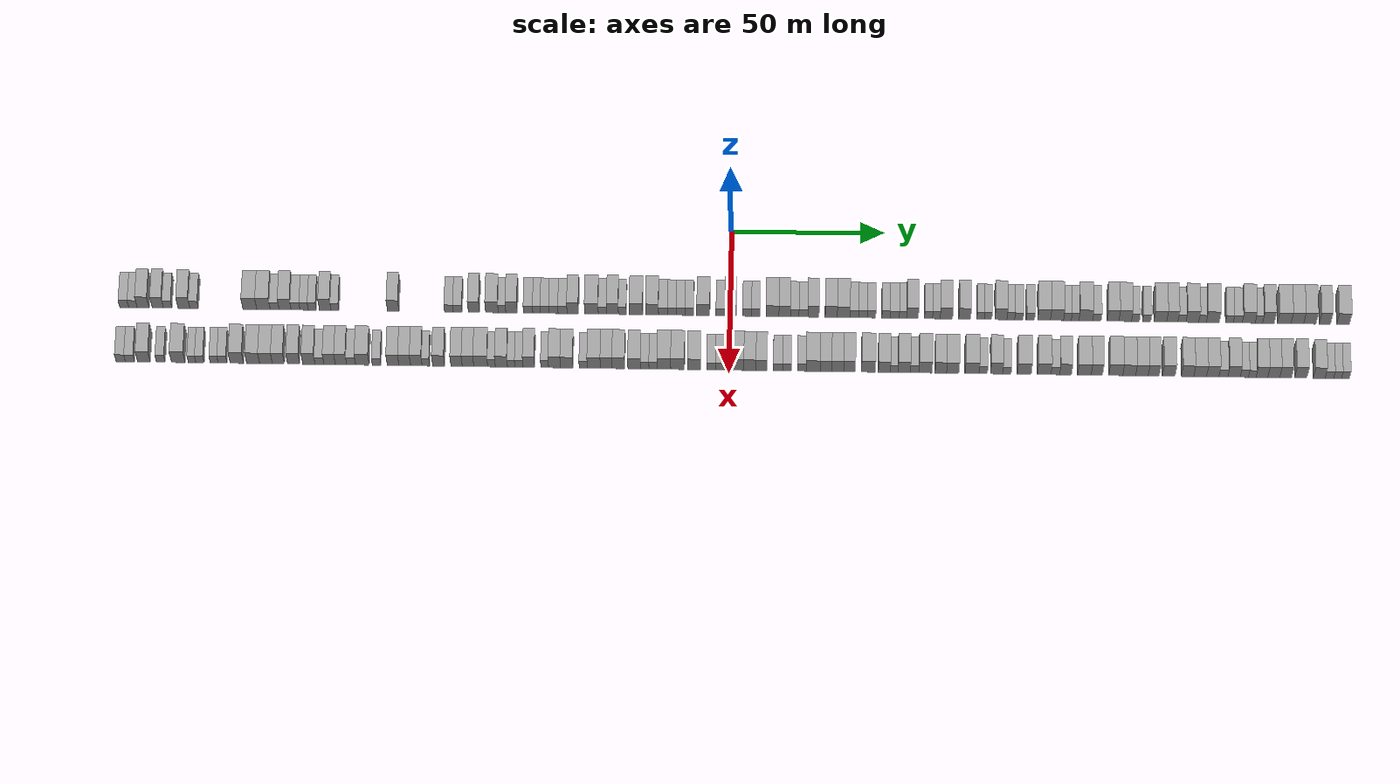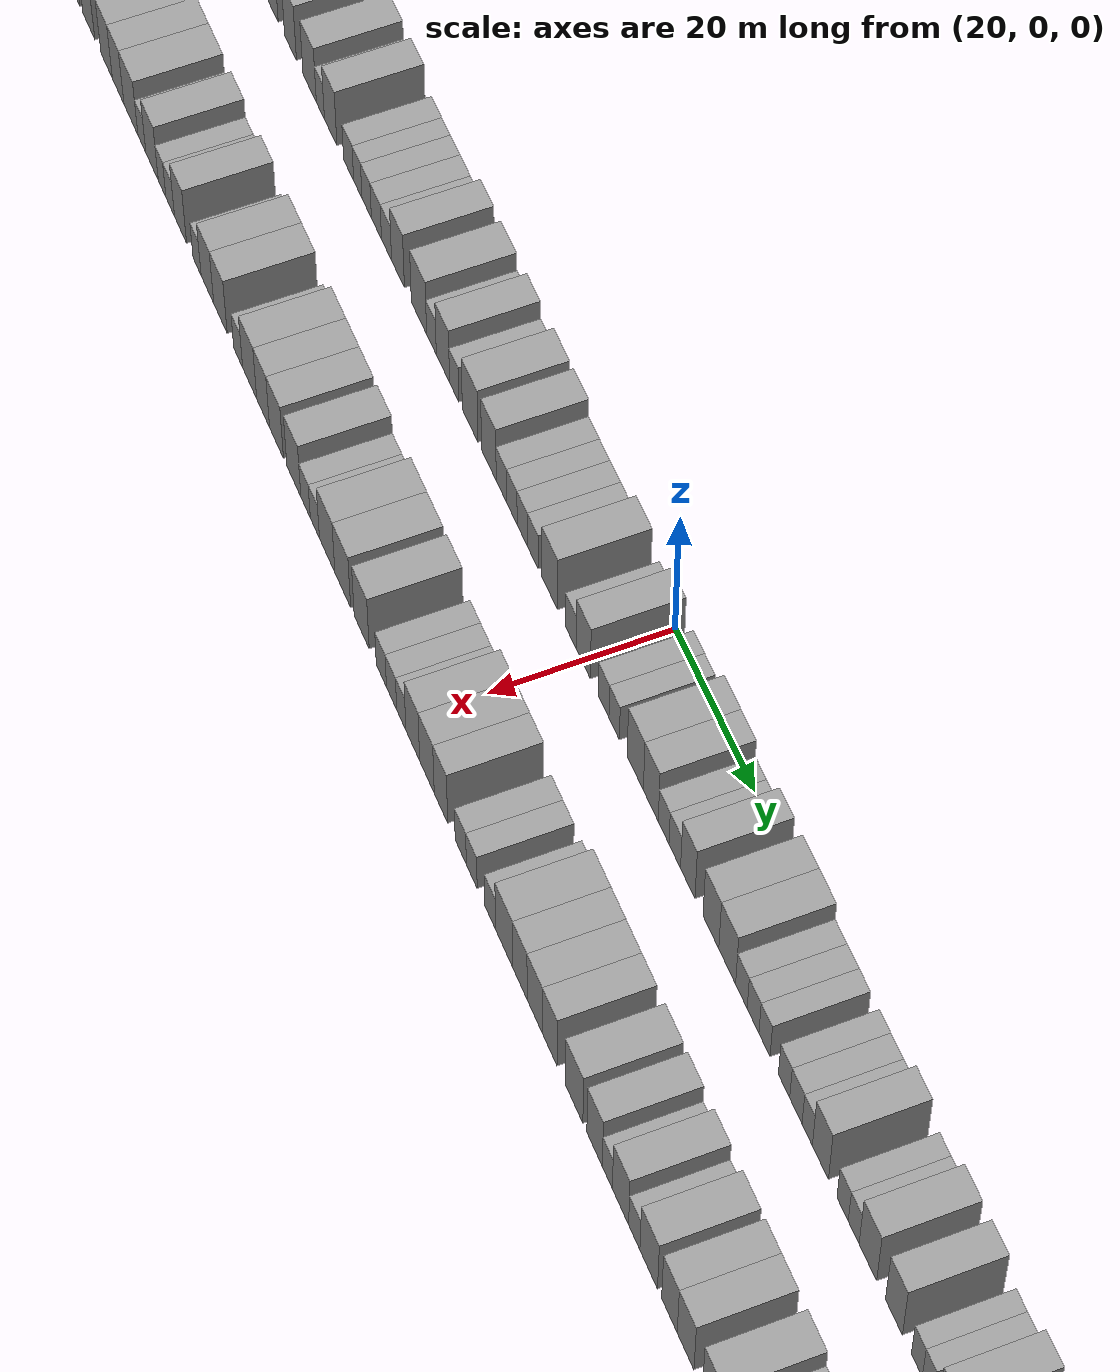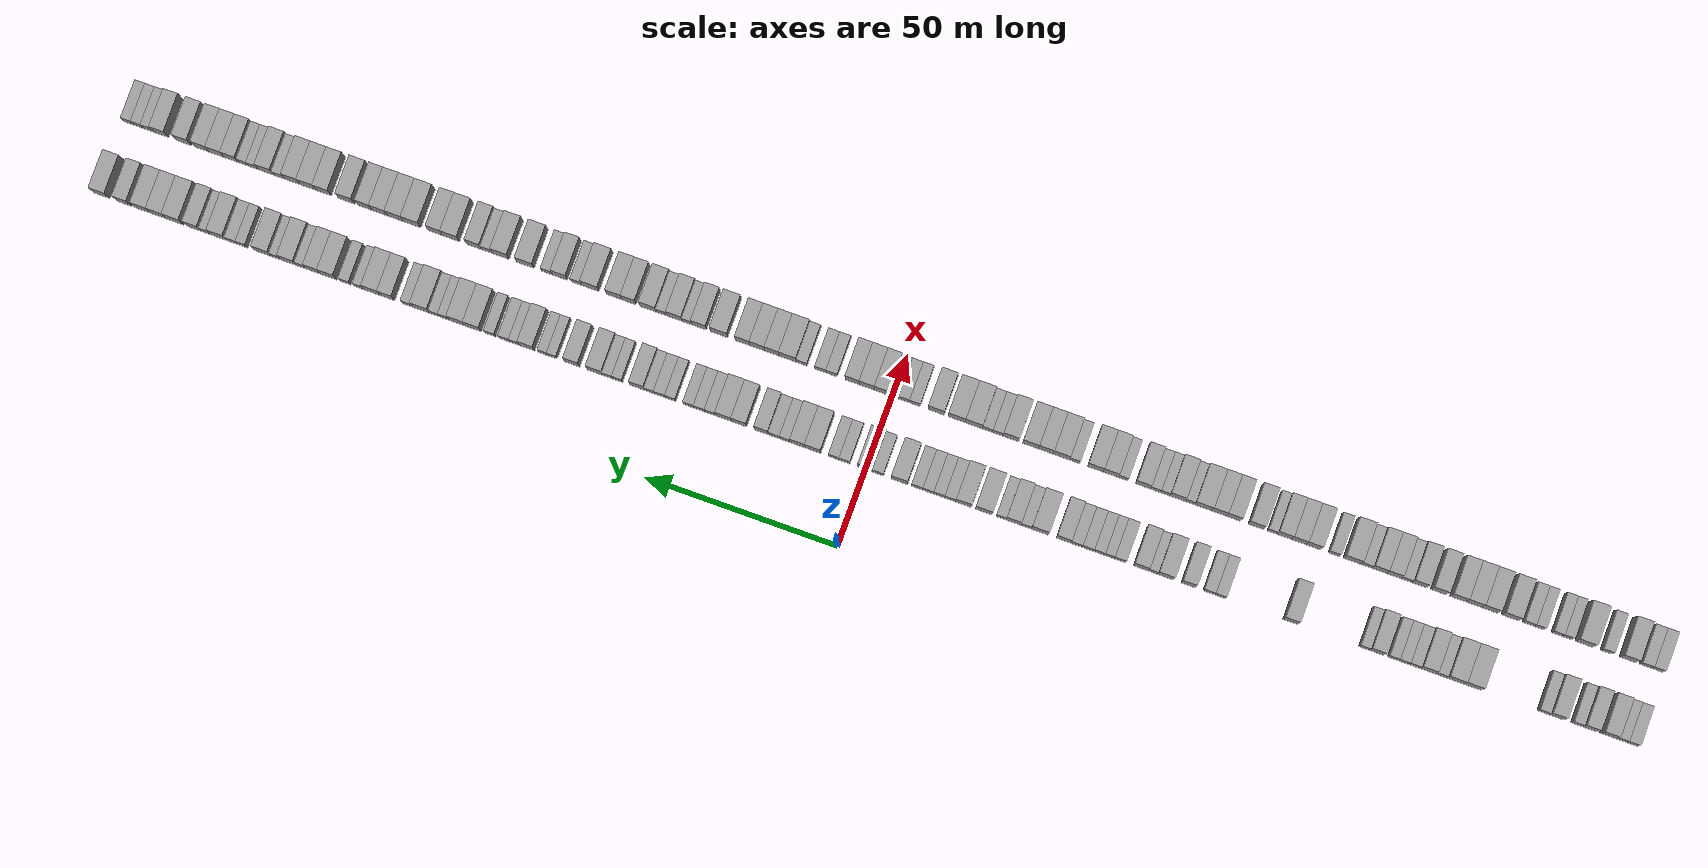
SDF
<sdf version="1.6">
 <world name="default">
  <scene>
   <sky><clouds><speed>12</speed></clouds></sky>
   <ambient>0.4 0.4 0.4 1</ambient>
   <background>0.7 0.7 0.7 1</background>
   <shadows>1</shadows>
  </scene>
  <gravity>0 0 -9.8066</gravity>
  <magnetic_field>6e-06 2.3e-05 -4.2e-05</magnetic_field>
  <physics default="0" name="default_physics" type="ode">
   <ode>
    <solver>
     <type>quick</type>
     <iters>10</iters>
     <sor>1.0</sor>
     <use_dynamic_moi_rescaling>0</use_dynamic_moi_rescaling>
    </solver>
    <constraints>
     <cfm>0</cfm>
     <erp>0.2</erp>
     <contact_max_correcting_vel>100</contact_max_correcting_vel>
     <contact_surface_layer>0.001</contact_surface_layer>
    </constraints>
   </ode>
   <max_step_size>0.004</max_step_size>
   <real_time_factor>1</real_time_factor>
   <real_time_update_rate>250</real_time_update_rate>
  </physics>
  <light name="sun" type="directional">
   <pose>0 0 10 0 0 0</pose>
   <diffuse>0.8 0.8 0.8 1</diffuse>
   <specular>0.2 0.2 0.2 1</specular>
   <attenuation>
    <range>1000</range>
    <constant>0.9</constant>
    <linear>0.01</linear>
    <quadratic>0.001</quadratic>
   </attenuation>
   <direction>-0.5 0.1 -0.9</direction>
  </light>
  <model name="building_1">
   <static>1</static>
   <pose>25.0000 -196.5424 0 0.000000 0.000000 0.000000</pose>
   <link name="link">
    <pose>0 0 3.00 0 0 0</pose>
    <collision name="collision"><geometry><box><size>10.0000 2.9151 6.0000</size></box></geometry></collision>
    <visual name="visual">
     <cast_shadows>0</cast_shadows>
     <geometry><box><size>10.0000 2.9151 6.0000</size></box></geometry>
     <material>
      <script>
       <uri>model://grey_wall/materials/scripts</uri>
       <uri>model://grey_wall/materials/textures</uri>
       <name>vrc/grey_wall</name>
      </script>
     </material>
    </visual>
   </link>
  </model>
  <model name="building_2">
   <static>1</static>
   <pose>25.0000 -193.7213 0 0.000000 0.000000 0.000000</pose>
   <link name="link">
    <pose>0 0 3.00 0 0 0</pose>
    <collision name="collision"><geometry><box><size>10.0000 2.7271 6.0000</size></box></geometry></collision>
    <visual name="visual">
     <cast_shadows>0</cast_shadows>
     <geometry><box><size>10.0000 2.7271 6.0000</size></box></geometry>
     <material>
      <script>
       <uri>model://grey_wall/materials/scripts</uri>
       <uri>model://grey_wall/materials/textures</uri>
       <name>vrc/grey_wall</name>
      </script>
     </material>
    </visual>
   </link>
  </model>
  <model name="building_3">
   <static>1</static>
   <pose>25.0000 -190.4169 0 0.000000 0.000000 0.000000</pose>
   <link name="link">
    <pose>0 0 4.50 0 0 0</pose>
    <collision name="collision"><geometry><box><size>10.0000 3.8818 9.0000</size></box></geometry></collision>
    <visual name="visual">
     <cast_shadows>0</cast_shadows>
     <geometry><box><size>10.0000 3.8818 9.0000</size></box></geometry>
     <material>
      <script>
       <uri>model://grey_wall/materials/scripts</uri>
       <uri>model://grey_wall/materials/textures</uri>
       <name>vrc/grey_wall</name>
      </script>
     </material>
    </visual>
   </link>
  </model>
  <model name="building_4">
   <static>1</static>
   <pose>25.0000 -185.6511 0 0.000000 0.000000 0.000000</pose>
   <link name="link">
    <pose>0 0 4.50 0 0 0</pose>
    <collision name="collision"><geometry><box><size>10.0000 3.6497 9.0000</size></box></geometry></collision>
    <visual name="visual">
     <cast_shadows>0</cast_shadows>
     <geometry><box><size>10.0000 3.6497 9.0000</size></box></geometry>
     <material>
      <script>
       <uri>model://grey_wall/materials/scripts</uri>
       <uri>model://grey_wall/materials/textures</uri>
       <name>vrc/grey_wall</name>
      </script>
     </material>
    </visual>
   </link>
  </model>
  <model name="building_5">
   <static>1</static>
   <pose>25.0000 -182.4479 0 0.000000 0.000000 0.000000</pose>
   <link name="link">
    <pose>0 0 3.00 0 0 0</pose>
    <collision name="collision"><geometry><box><size>10.0000 2.7566 6.0000</size></box></geometry></collision>
    <visual name="visual">
     <cast_shadows>0</cast_shadows>
     <geometry><box><size>10.0000 2.7566 6.0000</size></box></geometry>
     <material>
      <script>
       <uri>model://grey_wall/materials/scripts</uri>
       <uri>model://grey_wall/materials/textures</uri>
       <name>vrc/grey_wall</name>
      </script>
     </material>
    </visual>
   </link>
  </model>
  <model name="building_6">
   <static>1</static>
   <pose>25.0000 -177.1667 0 0.000000 0.000000 0.000000</pose>
   <link name="link">
    <pose>0 0 4.50 0 0 0</pose>
    <collision name="collision"><geometry><box><size>10.0000 3.8058 9.0000</size></box></geometry></collision>
    <visual name="visual">
     <cast_shadows>0</cast_shadows>
     <geometry><box><size>10.0000 3.8058 9.0000</size></box></geometry>
     <material>
      <script>
       <uri>model://grey_wall/materials/scripts</uri>
       <uri>model://grey_wall/materials/textures</uri>
       <name>vrc/grey_wall</name>
      </script>
     </material>
    </visual>
   </link>
  </model>
  <model name="building_7">
   <static>1</static>
   <pose>25.0000 -173.8585 0 0.000000 0.000000 0.000000</pose>
   <link name="link">
    <pose>0 0 3.00 0 0 0</pose>
    <collision name="collision"><geometry><box><size>10.0000 2.8106 6.0000</size></box></geometry></collision>
    <visual name="visual">
     <cast_shadows>0</cast_shadows>
     <geometry><box><size>10.0000 2.8106 6.0000</size></box></geometry>
     <material>
      <script>
       <uri>model://grey_wall/materials/scripts</uri>
       <uri>model://grey_wall/materials/textures</uri>
       <name>vrc/grey_wall</name>
      </script>
     </material>
    </visual>
   </link>
  </model>
  <model name="building_8">
   <static>1</static>
   <pose>25.0000 -155.7688 0 0.000000 0.000000 0.000000</pose>
   <link name="link">
    <pose>0 0 4.50 0 0 0</pose>
    <collision name="collision"><geometry><box><size>10.0000 4.4563 9.0000</size></box></geometry></collision>
    <visual name="visual">
     <cast_shadows>0</cast_shadows>
     <geometry><box><size>10.0000 4.4563 9.0000</size></box></geometry>
     <material>
      <script>
       <uri>model://grey_wall/materials/scripts</uri>
       <uri>model://grey_wall/materials/textures</uri>
       <name>vrc/grey_wall</name>
      </script>
     </material>
    </visual>
   </link>
  </model>
  <model name="building_9">
   <static>1</static>
   <pose>25.0000 -151.3571 0 0.000000 0.000000 0.000000</pose>
   <link name="link">
    <pose>0 0 4.50 0 0 0</pose>
    <collision name="collision"><geometry><box><size>10.0000 4.3670 9.0000</size></box></geometry></collision>
    <visual name="visual">
     <cast_shadows>0</cast_shadows>
     <geometry><box><size>10.0000 4.3670 9.0000</size></box></geometry>
     <material>
      <script>
       <uri>model://grey_wall/materials/scripts</uri>
       <uri>model://grey_wall/materials/textures</uri>
       <name>vrc/grey_wall</name>
      </script>
     </material>
    </visual>
   </link>
  </model>
  <model name="building_10">
   <static>1</static>
   <pose>25.0000 -147.7145 0 0.000000 0.000000 0.000000</pose>
   <link name="link">
    <pose>0 0 3.00 0 0 0</pose>
    <collision name="collision"><geometry><box><size>10.0000 2.9183 6.0000</size></box></geometry></collision>
    <visual name="visual">
     <cast_shadows>0</cast_shadows>
     <geometry><box><size>10.0000 2.9183 6.0000</size></box></geometry>
     <material>
      <script>
       <uri>model://grey_wall/materials/scripts</uri>
       <uri>model://grey_wall/materials/textures</uri>
       <name>vrc/grey_wall</name>
      </script>
     </material>
    </visual>
   </link>
  </model>
  <model name="building_11">
   <static>1</static>
   <pose>25.0000 -144.3150 0 0.000000 0.000000 0.000000</pose>
   <link name="link">
    <pose>0 0 4.50 0 0 0</pose>
    <collision name="collision"><geometry><box><size>10.0000 3.8806 9.0000</size></box></geometry></collision>
    <visual name="visual">
     <cast_shadows>0</cast_shadows>
     <geometry><box><size>10.0000 3.8806 9.0000</size></box></geometry>
     <material>
      <script>
       <uri>model://grey_wall/materials/scripts</uri>
       <uri>model://grey_wall/materials/textures</uri>
       <name>vrc/grey_wall</name>
      </script>
     </material>
    </visual>
   </link>
  </model>
  <model name="building_12">
   <static>1</static>
   <pose>25.0000 -140.9301 0 0.000000 0.000000 0.000000</pose>
   <link name="link">
    <pose>0 0 3.00 0 0 0</pose>
    <collision name="collision"><geometry><box><size>10.0000 2.8893 6.0000</size></box></geometry></collision>
    <visual name="visual">
     <cast_shadows>0</cast_shadows>
     <geometry><box><size>10.0000 2.8893 6.0000</size></box></geometry>
     <material>
      <script>
       <uri>model://grey_wall/materials/scripts</uri>
       <uri>model://grey_wall/materials/textures</uri>
       <name>vrc/grey_wall</name>
      </script>
     </material>
    </visual>
   </link>
  </model>
  <model name="building_13">
   <static>1</static>
   <pose>25.0000 -138.1441 0 0.000000 0.000000 0.000000</pose>
   <link name="link">
    <pose>0 0 3.00 0 0 0</pose>
    <collision name="collision"><geometry><box><size>10.0000 2.6826 6.0000</size></box></geometry></collision>
    <visual name="visual">
     <cast_shadows>0</cast_shadows>
     <geometry><box><size>10.0000 2.6826 6.0000</size></box></geometry>
     <material>
      <script>
       <uri>model://grey_wall/materials/scripts</uri>
       <uri>model://grey_wall/materials/textures</uri>
       <name>vrc/grey_wall</name>
      </script>
     </material>
    </visual>
   </link>
  </model>
  <model name="building_14">
   <static>1</static>
   <pose>25.0000 -135.4842 0 0.000000 0.000000 0.000000</pose>
   <link name="link">
    <pose>0 0 3.00 0 0 0</pose>
    <collision name="collision"><geometry><box><size>10.0000 2.6374 6.0000</size></box></geometry></collision>
    <visual name="visual">
     <cast_shadows>0</cast_shadows>
     <geometry><box><size>10.0000 2.6374 6.0000</size></box></geometry>
     <material>
      <script>
       <uri>model://grey_wall/materials/scripts</uri>
       <uri>model://grey_wall/materials/textures</uri>
       <name>vrc/grey_wall</name>
      </script>
     </material>
    </visual>
   </link>
  </model>
  <model name="building_15">
   <static>1</static>
   <pose>25.0000 -131.2975 0 0.000000 0.000000 0.000000</pose>
   <link name="link">
    <pose>0 0 4.50 0 0 0</pose>
    <collision name="collision"><geometry><box><size>10.0000 3.7358 9.0000</size></box></geometry></collision>
    <visual name="visual">
     <cast_shadows>0</cast_shadows>
     <geometry><box><size>10.0000 3.7358 9.0000</size></box></geometry>
     <material>
      <script>
       <uri>model://grey_wall/materials/scripts</uri>
       <uri>model://grey_wall/materials/textures</uri>
       <name>vrc/grey_wall</name>
      </script>
     </material>
    </visual>
   </link>
  </model>
  <model name="building_16">
   <static>1</static>
   <pose>25.0000 -128.1174 0 0.000000 0.000000 0.000000</pose>
   <link name="link">
    <pose>0 0 3.00 0 0 0</pose>
    <collision name="collision"><geometry><box><size>10.0000 2.6244 6.0000</size></box></geometry></collision>
    <visual name="visual">
     <cast_shadows>0</cast_shadows>
     <geometry><box><size>10.0000 2.6244 6.0000</size></box></geometry>
     <material>
      <script>
       <uri>model://grey_wall/materials/scripts</uri>
       <uri>model://grey_wall/materials/textures</uri>
       <name>vrc/grey_wall</name>
      </script>
     </material>
    </visual>
   </link>
  </model>
  <model name="building_17">
   <static>1</static>
   <pose>25.0000 -109.2141 0 0.000000 0.000000 0.000000</pose>
   <link name="link">
    <pose>0 0 4.50 0 0 0</pose>
    <collision name="collision"><geometry><box><size>10.0000 3.7274 9.0000</size></box></geometry></collision>
    <visual name="visual">
     <cast_shadows>0</cast_shadows>
     <geometry><box><size>10.0000 3.7274 9.0000</size></box></geometry>
     <material>
      <script>
       <uri>model://grey_wall/materials/scripts</uri>
       <uri>model://grey_wall/materials/textures</uri>
       <name>vrc/grey_wall</name>
      </script>
     </material>
    </visual>
   </link>
  </model>
  <model name="building_18">
   <static>1</static>
   <pose>25.0000 -91.1532 0 0.000000 0.000000 0.000000</pose>
   <link name="link">
    <pose>0 0 3.00 0 0 0</pose>
    <collision name="collision"><geometry><box><size>10.0000 2.7981 6.0000</size></box></geometry></collision>
    <visual name="visual">
     <cast_shadows>0</cast_shadows>
     <geometry><box><size>10.0000 2.7981 6.0000</size></box></geometry>
     <material>
      <script>
       <uri>model://grey_wall/materials/scripts</uri>
       <uri>model://grey_wall/materials/textures</uri>
       <name>vrc/grey_wall</name>
      </script>
     </material>
    </visual>
   </link>
  </model>
  <model name="building_19">
   <static>1</static>
   <pose>25.0000 -88.2981 0 0.000000 0.000000 0.000000</pose>
   <link name="link">
    <pose>0 0 3.00 0 0 0</pose>
    <collision name="collision"><geometry><box><size>10.0000 2.9122 6.0000</size></box></geometry></collision>
    <visual name="visual">
     <cast_shadows>0</cast_shadows>
     <geometry><box><size>10.0000 2.9122 6.0000</size></box></geometry>
     <material>
      <script>
       <uri>model://grey_wall/materials/scripts</uri>
       <uri>model://grey_wall/materials/textures</uri>
       <name>vrc/grey_wall</name>
      </script>
     </material>
    </visual>
   </link>
  </model>
  <model name="building_20">
   <static>1</static>
   <pose>25.0000 -83.0291 0 0.000000 0.000000 0.000000</pose>
   <link name="link">
    <pose>0 0 4.50 0 0 0</pose>
    <collision name="collision"><geometry><box><size>10.0000 3.6257 9.0000</size></box></geometry></collision>
    <visual name="visual">
     <cast_shadows>0</cast_shadows>
     <geometry><box><size>10.0000 3.6257 9.0000</size></box></geometry>
     <material>
      <script>
       <uri>model://grey_wall/materials/scripts</uri>
       <uri>model://grey_wall/materials/textures</uri>
       <name>vrc/grey_wall</name>
      </script>
     </material>
    </visual>
   </link>
  </model>
  <model name="building_21">
   <static>1</static>
   <pose>25.0000 -77.1850 0 0.000000 0.000000 0.000000</pose>
   <link name="link">
    <pose>0 0 4.50 0 0 0</pose>
    <collision name="collision"><geometry><box><size>10.0000 4.0627 9.0000</size></box></geometry></collision>
    <visual name="visual">
     <cast_shadows>0</cast_shadows>
     <geometry><box><size>10.0000 4.0627 9.0000</size></box></geometry>
     <material>
      <script>
       <uri>model://grey_wall/materials/scripts</uri>
       <uri>model://grey_wall/materials/textures</uri>
       <name>vrc/grey_wall</name>
      </script>
     </material>
    </visual>
   </link>
  </model>
  <model name="building_22">
   <static>1</static>
   <pose>25.0000 -73.9256 0 0.000000 0.000000 0.000000</pose>
   <link name="link">
    <pose>0 0 3.00 0 0 0</pose>
    <collision name="collision"><geometry><box><size>10.0000 2.4560 6.0000</size></box></geometry></collision>
    <visual name="visual">
     <cast_shadows>0</cast_shadows>
     <geometry><box><size>10.0000 2.4560 6.0000</size></box></geometry>
     <material>
      <script>
       <uri>model://grey_wall/materials/scripts</uri>
       <uri>model://grey_wall/materials/textures</uri>
       <name>vrc/grey_wall</name>
      </script>
     </material>
    </visual>
   </link>
  </model>
  <model name="building_23">
   <static>1</static>
   <pose>25.0000 -70.8167 0 0.000000 0.000000 0.000000</pose>
   <link name="link">
    <pose>0 0 4.50 0 0 0</pose>
    <collision name="collision"><geometry><box><size>10.0000 3.7619 9.0000</size></box></geometry></collision>
    <visual name="visual">
     <cast_shadows>0</cast_shadows>
     <geometry><box><size>10.0000 3.7619 9.0000</size></box></geometry>
     <material>
      <script>
       <uri>model://grey_wall/materials/scripts</uri>
       <uri>model://grey_wall/materials/textures</uri>
       <name>vrc/grey_wall</name>
      </script>
     </material>
    </visual>
   </link>
  </model>
  <model name="building_24">
   <static>1</static>
   <pose>25.0000 -65.4381 0 0.000000 0.000000 0.000000</pose>
   <link name="link">
    <pose>0 0 3.00 0 0 0</pose>
    <collision name="collision"><geometry><box><size>10.0000 2.9952 6.0000</size></box></geometry></collision>
    <visual name="visual">
     <cast_shadows>0</cast_shadows>
     <geometry><box><size>10.0000 2.9952 6.0000</size></box></geometry>
     <material>
      <script>
       <uri>model://grey_wall/materials/scripts</uri>
       <uri>model://grey_wall/materials/textures</uri>
       <name>vrc/grey_wall</name>
      </script>
     </material>
    </visual>
   </link>
  </model>
  <model name="building_25">
   <static>1</static>
   <pose>25.0000 -62.7104 0 0.000000 0.000000 0.000000</pose>
   <link name="link">
    <pose>0 0 3.00 0 0 0</pose>
    <collision name="collision"><geometry><box><size>10.0000 2.4601 6.0000</size></box></geometry></collision>
    <visual name="visual">
     <cast_shadows>0</cast_shadows>
     <geometry><box><size>10.0000 2.4601 6.0000</size></box></geometry>
     <material>
      <script>
       <uri>model://grey_wall/materials/scripts</uri>
       <uri>model://grey_wall/materials/textures</uri>
       <name>vrc/grey_wall</name>
      </script>
     </material>
    </visual>
   </link>
  </model>
  <model name="building_26">
   <static>1</static>
   <pose>25.0000 -60.0900 0 0.000000 0.000000 0.000000</pose>
   <link name="link">
    <pose>0 0 3.00 0 0 0</pose>
    <collision name="collision"><geometry><box><size>10.0000 2.7807 6.0000</size></box></geometry></collision>
    <visual name="visual">
     <cast_shadows>0</cast_shadows>
     <geometry><box><size>10.0000 2.7807 6.0000</size></box></geometry>
     <material>
      <script>
       <uri>model://grey_wall/materials/scripts</uri>
       <uri>model://grey_wall/materials/textures</uri>
       <name>vrc/grey_wall</name>
      </script>
     </material>
    </visual>
   </link>
  </model>
  <model name="building_27">
   <static>1</static>
   <pose>25.0000 -57.2207 0 0.000000 0.000000 0.000000</pose>
   <link name="link">
    <pose>0 0 3.00 0 0 0</pose>
    <collision name="collision"><geometry><box><size>10.0000 2.9579 6.0000</size></box></geometry></collision>
    <visual name="visual">
     <cast_shadows>0</cast_shadows>
     <geometry><box><size>10.0000 2.9579 6.0000</size></box></geometry>
     <material>
      <script>
       <uri>model://grey_wall/materials/scripts</uri>
       <uri>model://grey_wall/materials/textures</uri>
       <name>vrc/grey_wall</name>
      </script>
     </material>
    </visual>
   </link>
  </model>
  <model name="building_28">
   <static>1</static>
   <pose>25.0000 -54.2702 0 0.000000 0.000000 0.000000</pose>
   <link name="link">
    <pose>0 0 3.00 0 0 0</pose>
    <collision name="collision"><geometry><box><size>10.0000 2.9431 6.0000</size></box></geometry></collision>
    <visual name="visual">
     <cast_shadows>0</cast_shadows>
     <geometry><box><size>10.0000 2.9431 6.0000</size></box></geometry>
     <material>
      <script>
       <uri>model://grey_wall/materials/scripts</uri>
       <uri>model://grey_wall/materials/textures</uri>
       <name>vrc/grey_wall</name>
      </script>
     </material>
    </visual>
   </link>
  </model>
  <model name="building_29">
   <static>1</static>
   <pose>25.0000 -50.9365 0 0.000000 0.000000 0.000000</pose>
   <link name="link">
    <pose>0 0 4.50 0 0 0</pose>
    <collision name="collision"><geometry><box><size>10.0000 3.7242 9.0000</size></box></geometry></collision>
    <visual name="visual">
     <cast_shadows>0</cast_shadows>
     <geometry><box><size>10.0000 3.7242 9.0000</size></box></geometry>
     <material>
      <script>
       <uri>model://grey_wall/materials/scripts</uri>
       <uri>model://grey_wall/materials/textures</uri>
       <name>vrc/grey_wall</name>
      </script>
     </material>
    </visual>
   </link>
  </model>
  <model name="building_30">
   <static>1</static>
   <pose>25.0000 -44.8834 0 0.000000 0.000000 0.000000</pose>
   <link name="link">
    <pose>0 0 4.50 0 0 0</pose>
    <collision name="collision"><geometry><box><size>10.0000 4.3821 9.0000</size></box></geometry></collision>
    <visual name="visual">
     <cast_shadows>0</cast_shadows>
     <geometry><box><size>10.0000 4.3821 9.0000</size></box></geometry>
     <material>
      <script>
       <uri>model://grey_wall/materials/scripts</uri>
       <uri>model://grey_wall/materials/textures</uri>
       <name>vrc/grey_wall</name>
      </script>
     </material>
    </visual>
   </link>
  </model>
  <model name="building_31">
   <static>1</static>
   <pose>25.0000 -41.3142 0 0.000000 0.000000 0.000000</pose>
   <link name="link">
    <pose>0 0 3.00 0 0 0</pose>
    <collision name="collision"><geometry><box><size>10.0000 2.7561 6.0000</size></box></geometry></collision>
    <visual name="visual">
     <cast_shadows>0</cast_shadows>
     <geometry><box><size>10.0000 2.7561 6.0000</size></box></geometry>
     <material>
      <script>
       <uri>model://grey_wall/materials/scripts</uri>
       <uri>model://grey_wall/materials/textures</uri>
       <name>vrc/grey_wall</name>
      </script>
     </material>
    </visual>
   </link>
  </model>
  <model name="building_32">
   <static>1</static>
   <pose>25.0000 -38.0559 0 0.000000 0.000000 0.000000</pose>
   <link name="link">
    <pose>0 0 4.50 0 0 0</pose>
    <collision name="collision"><geometry><box><size>10.0000 3.7605 9.0000</size></box></geometry></collision>
    <visual name="visual">
     <cast_shadows>0</cast_shadows>
     <geometry><box><size>10.0000 3.7605 9.0000</size></box></geometry>
     <material>
      <script>
       <uri>model://grey_wall/materials/scripts</uri>
       <uri>model://grey_wall/materials/textures</uri>
       <name>vrc/grey_wall</name>
      </script>
     </material>
    </visual>
   </link>
  </model>
  <model name="building_33">
   <static>1</static>
   <pose>25.0000 -34.8856 0 0.000000 0.000000 0.000000</pose>
   <link name="link">
    <pose>0 0 3.00 0 0 0</pose>
    <collision name="collision"><geometry><box><size>10.0000 2.5803 6.0000</size></box></geometry></collision>
    <visual name="visual">
     <cast_shadows>0</cast_shadows>
     <geometry><box><size>10.0000 2.5803 6.0000</size></box></geometry>
     <material>
      <script>
       <uri>model://grey_wall/materials/scripts</uri>
       <uri>model://grey_wall/materials/textures</uri>
       <name>vrc/grey_wall</name>
      </script>
     </material>
    </visual>
   </link>
  </model>
  <model name="building_34">
   <static>1</static>
   <pose>25.0000 -30.4184 0 0.000000 0.000000 0.000000</pose>
   <link name="link">
    <pose>0 0 4.50 0 0 0</pose>
    <collision name="collision"><geometry><box><size>10.0000 4.3540 9.0000</size></box></geometry></collision>
    <visual name="visual">
     <cast_shadows>0</cast_shadows>
     <geometry><box><size>10.0000 4.3540 9.0000</size></box></geometry>
     <material>
      <script>
       <uri>model://grey_wall/materials/scripts</uri>
       <uri>model://grey_wall/materials/textures</uri>
       <name>vrc/grey_wall</name>
      </script>
     </material>
    </visual>
   </link>
  </model>
  <model name="building_35">
   <static>1</static>
   <pose>25.0000 -25.2072 0 0.000000 0.000000 0.000000</pose>
   <link name="link">
    <pose>0 0 4.50 0 0 0</pose>
    <collision name="collision"><geometry><box><size>10.0000 4.0686 9.0000</size></box></geometry></collision>
    <visual name="visual">
     <cast_shadows>0</cast_shadows>
     <geometry><box><size>10.0000 4.0686 9.0000</size></box></geometry>
     <material>
      <script>
       <uri>model://grey_wall/materials/scripts</uri>
       <uri>model://grey_wall/materials/textures</uri>
       <name>vrc/grey_wall</name>
      </script>
     </material>
    </visual>
   </link>
  </model>
  <model name="building_36">
   <static>1</static>
   <pose>25.0000 -21.7188 0 0.000000 0.000000 0.000000</pose>
   <link name="link">
    <pose>0 0 3.00 0 0 0</pose>
    <collision name="collision"><geometry><box><size>10.0000 2.9082 6.0000</size></box></geometry></collision>
    <visual name="visual">
     <cast_shadows>0</cast_shadows>
     <geometry><box><size>10.0000 2.9082 6.0000</size></box></geometry>
     <material>
      <script>
       <uri>model://grey_wall/materials/scripts</uri>
       <uri>model://grey_wall/materials/textures</uri>
       <name>vrc/grey_wall</name>
      </script>
     </material>
    </visual>
   </link>
  </model>
  <model name="building_37">
   <static>1</static>
   <pose>25.0000 -18.8592 0 0.000000 0.000000 0.000000</pose>
   <link name="link">
    <pose>0 0 3.00 0 0 0</pose>
    <collision name="collision"><geometry><box><size>10.0000 2.8110 6.0000</size></box></geometry></collision>
    <visual name="visual">
     <cast_shadows>0</cast_shadows>
     <geometry><box><size>10.0000 2.8110 6.0000</size></box></geometry>
     <material>
      <script>
       <uri>model://grey_wall/materials/scripts</uri>
       <uri>model://grey_wall/materials/textures</uri>
       <name>vrc/grey_wall</name>
      </script>
     </material>
    </visual>
   </link>
  </model>
  <model name="building_38">
   <static>1</static>
   <pose>25.0000 -16.0442 0 0.000000 0.000000 0.000000</pose>
   <link name="link">
    <pose>0 0 3.00 0 0 0</pose>
    <collision name="collision"><geometry><box><size>10.0000 2.8189 6.0000</size></box></geometry></collision>
    <visual name="visual">
     <cast_shadows>0</cast_shadows>
     <geometry><box><size>10.0000 2.8189 6.0000</size></box></geometry>
     <material>
      <script>
       <uri>model://grey_wall/materials/scripts</uri>
       <uri>model://grey_wall/materials/textures</uri>
       <name>vrc/grey_wall</name>
      </script>
     </material>
    </visual>
   </link>
  </model>
  <model name="building_39">
   <static>1</static>
   <pose>25.0000 -13.1848 0 0.000000 0.000000 0.000000</pose>
   <link name="link">
    <pose>0 0 3.00 0 0 0</pose>
    <collision name="collision"><geometry><box><size>10.0000 2.9000 6.0000</size></box></geometry></collision>
    <visual name="visual">
     <cast_shadows>0</cast_shadows>
     <geometry><box><size>10.0000 2.9000 6.0000</size></box></geometry>
     <material>
      <script>
       <uri>model://grey_wall/materials/scripts</uri>
       <uri>model://grey_wall/materials/textures</uri>
       <name>vrc/grey_wall</name>
      </script>
     </material>
    </visual>
   </link>
  </model>
  <model name="building_40">
   <static>1</static>
   <pose>25.0000 -8.6283 0 0.000000 0.000000 0.000000</pose>
   <link name="link">
    <pose>0 0 4.50 0 0 0</pose>
    <collision name="collision"><geometry><box><size>10.0000 4.2129 9.0000</size></box></geometry></collision>
    <visual name="visual">
     <cast_shadows>0</cast_shadows>
     <geometry><box><size>10.0000 4.2129 9.0000</size></box></geometry>
     <material>
      <script>
       <uri>model://grey_wall/materials/scripts</uri>
       <uri>model://grey_wall/materials/textures</uri>
       <name>vrc/grey_wall</name>
      </script>
     </material>
    </visual>
   </link>
  </model>
  <model name="building_41">
   <static>1</static>
   <pose>25.0000 -3.0565 0 0.000000 0.000000 0.000000</pose>
   <link name="link">
    <pose>0 0 3.00 0 0 0</pose>
    <collision name="collision"><geometry><box><size>10.0000 2.9308 6.0000</size></box></geometry></collision>
    <visual name="visual">
     <cast_shadows>0</cast_shadows>
     <geometry><box><size>10.0000 2.9308 6.0000</size></box></geometry>
     <material>
      <script>
       <uri>model://grey_wall/materials/scripts</uri>
       <uri>model://grey_wall/materials/textures</uri>
       <name>vrc/grey_wall</name>
      </script>
     </material>
    </visual>
   </link>
  </model>
  <model name="building_42">
   <static>1</static>
   <pose>25.0000 0.2762 0 0.000000 0.000000 0.000000</pose>
   <link name="link">
    <pose>0 0 4.50 0 0 0</pose>
    <collision name="collision"><geometry><box><size>10.0000 3.7345 9.0000</size></box></geometry></collision>
    <visual name="visual">
     <cast_shadows>0</cast_shadows>
     <geometry><box><size>10.0000 3.7345 9.0000</size></box></geometry>
     <material>
      <script>
       <uri>model://grey_wall/materials/scripts</uri>
       <uri>model://grey_wall/materials/textures</uri>
       <name>vrc/grey_wall</name>
      </script>
     </material>
    </visual>
   </link>
  </model>
  <model name="building_43">
   <static>1</static>
   <pose>25.0000 5.5647 0 0.000000 0.000000 0.000000</pose>
   <link name="link">
    <pose>0 0 3.00 0 0 0</pose>
    <collision name="collision"><geometry><box><size>10.0000 2.8424 6.0000</size></box></geometry></collision>
    <visual name="visual">
     <cast_shadows>0</cast_shadows>
     <geometry><box><size>10.0000 2.8424 6.0000</size></box></geometry>
     <material>
      <script>
       <uri>model://grey_wall/materials/scripts</uri>
       <uri>model://grey_wall/materials/textures</uri>
       <name>vrc/grey_wall</name>
      </script>
     </material>
    </visual>
   </link>
  </model>
  <model name="building_44">
   <static>1</static>
   <pose>25.0000 8.3431 0 0.000000 0.000000 0.000000</pose>
   <link name="link">
    <pose>0 0 3.00 0 0 0</pose>
    <collision name="collision"><geometry><box><size>10.0000 2.7145 6.0000</size></box></geometry></collision>
    <visual name="visual">
     <cast_shadows>0</cast_shadows>
     <geometry><box><size>10.0000 2.7145 6.0000</size></box></geometry>
     <material>
      <script>
       <uri>model://grey_wall/materials/scripts</uri>
       <uri>model://grey_wall/materials/textures</uri>
       <name>vrc/grey_wall</name>
      </script>
     </material>
    </visual>
   </link>
  </model>
  <model name="building_45">
   <static>1</static>
   <pose>25.0000 13.7788 0 0.000000 0.000000 0.000000</pose>
   <link name="link">
    <pose>0 0 4.50 0 0 0</pose>
    <collision name="collision"><geometry><box><size>10.0000 4.1567 9.0000</size></box></geometry></collision>
    <visual name="visual">
     <cast_shadows>0</cast_shadows>
     <geometry><box><size>10.0000 4.1567 9.0000</size></box></geometry>
     <material>
      <script>
       <uri>model://grey_wall/materials/scripts</uri>
       <uri>model://grey_wall/materials/textures</uri>
       <name>vrc/grey_wall</name>
      </script>
     </material>
    </visual>
   </link>
  </model>
  <model name="building_46">
   <static>1</static>
   <pose>25.0000 17.7492 0 0.000000 0.000000 0.000000</pose>
   <link name="link">
    <pose>0 0 4.50 0 0 0</pose>
    <collision name="collision"><geometry><box><size>10.0000 3.7842 9.0000</size></box></geometry></collision>
    <visual name="visual">
     <cast_shadows>0</cast_shadows>
     <geometry><box><size>10.0000 3.7842 9.0000</size></box></geometry>
     <material>
      <script>
       <uri>model://grey_wall/materials/scripts</uri>
       <uri>model://grey_wall/materials/textures</uri>
       <name>vrc/grey_wall</name>
      </script>
     </material>
    </visual>
   </link>
  </model>
  <model name="building_47">
   <static>1</static>
   <pose>25.0000 20.9983 0 0.000000 0.000000 0.000000</pose>
   <link name="link">
    <pose>0 0 3.00 0 0 0</pose>
    <collision name="collision"><geometry><box><size>10.0000 2.7140 6.0000</size></box></geometry></collision>
    <visual name="visual">
     <cast_shadows>0</cast_shadows>
     <geometry><box><size>10.0000 2.7140 6.0000</size></box></geometry>
     <material>
      <script>
       <uri>model://grey_wall/materials/scripts</uri>
       <uri>model://grey_wall/materials/textures</uri>
       <name>vrc/grey_wall</name>
      </script>
     </material>
    </visual>
   </link>
  </model>
  <model name="building_48">
   <static>1</static>
   <pose>25.0000 23.8133 0 0.000000 0.000000 0.000000</pose>
   <link name="link">
    <pose>0 0 3.00 0 0 0</pose>
    <collision name="collision"><geometry><box><size>10.0000 2.9159 6.0000</size></box></geometry></collision>
    <visual name="visual">
     <cast_shadows>0</cast_shadows>
     <geometry><box><size>10.0000 2.9159 6.0000</size></box></geometry>
     <material>
      <script>
       <uri>model://grey_wall/materials/scripts</uri>
       <uri>model://grey_wall/materials/textures</uri>
       <name>vrc/grey_wall</name>
      </script>
     </material>
    </visual>
   </link>
  </model>
  <model name="building_49">
   <static>1</static>
   <pose>25.0000 27.0714 0 0.000000 0.000000 0.000000</pose>
   <link name="link">
    <pose>0 0 4.50 0 0 0</pose>
    <collision name="collision"><geometry><box><size>10.0000 3.6002 9.0000</size></box></geometry></collision>
    <visual name="visual">
     <cast_shadows>0</cast_shadows>
     <geometry><box><size>10.0000 3.6002 9.0000</size></box></geometry>
     <material>
      <script>
       <uri>model://grey_wall/materials/scripts</uri>
       <uri>model://grey_wall/materials/textures</uri>
       <name>vrc/grey_wall</name>
      </script>
     </material>
    </visual>
   </link>
  </model>
  <model name="building_50">
   <static>1</static>
   <pose>25.0000 32.8198 0 0.000000 0.000000 0.000000</pose>
   <link name="link">
    <pose>0 0 4.50 0 0 0</pose>
    <collision name="collision"><geometry><box><size>10.0000 3.8966 9.0000</size></box></geometry></collision>
    <visual name="visual">
     <cast_shadows>0</cast_shadows>
     <geometry><box><size>10.0000 3.8966 9.0000</size></box></geometry>
     <material>
      <script>
       <uri>model://grey_wall/materials/scripts</uri>
       <uri>model://grey_wall/materials/textures</uri>
       <name>vrc/grey_wall</name>
      </script>
     </material>
    </visual>
   </link>
  </model>
  <model name="building_51">
   <static>1</static>
   <pose>25.0000 36.8299 0 0.000000 0.000000 0.000000</pose>
   <link name="link">
    <pose>0 0 4.50 0 0 0</pose>
    <collision name="collision"><geometry><box><size>10.0000 4.1238 9.0000</size></box></geometry></collision>
    <visual name="visual">
     <cast_shadows>0</cast_shadows>
     <geometry><box><size>10.0000 4.1238 9.0000</size></box></geometry>
     <material>
      <script>
       <uri>model://grey_wall/materials/scripts</uri>
       <uri>model://grey_wall/materials/textures</uri>
       <name>vrc/grey_wall</name>
      </script>
     </material>
    </visual>
   </link>
  </model>
  <model name="building_52">
   <static>1</static>
   <pose>25.0000 40.3055 0 0.000000 0.000000 0.000000</pose>
   <link name="link">
    <pose>0 0 3.00 0 0 0</pose>
    <collision name="collision"><geometry><box><size>10.0000 2.8273 6.0000</size></box></geometry></collision>
    <visual name="visual">
     <cast_shadows>0</cast_shadows>
     <geometry><box><size>10.0000 2.8273 6.0000</size></box></geometry>
     <material>
      <script>
       <uri>model://grey_wall/materials/scripts</uri>
       <uri>model://grey_wall/materials/textures</uri>
       <name>vrc/grey_wall</name>
      </script>
     </material>
    </visual>
   </link>
  </model>
  <model name="building_53">
   <static>1</static>
   <pose>25.0000 43.1395 0 0.000000 0.000000 0.000000</pose>
   <link name="link">
    <pose>0 0 3.00 0 0 0</pose>
    <collision name="collision"><geometry><box><size>10.0000 2.8408 6.0000</size></box></geometry></collision>
    <visual name="visual">
     <cast_shadows>0</cast_shadows>
     <geometry><box><size>10.0000 2.8408 6.0000</size></box></geometry>
     <material>
      <script>
       <uri>model://grey_wall/materials/scripts</uri>
       <uri>model://grey_wall/materials/textures</uri>
       <name>vrc/grey_wall</name>
      </script>
     </material>
    </visual>
   </link>
  </model>
  <model name="building_54">
   <static>1</static>
   <pose>25.0000 45.9020 0 0.000000 0.000000 0.000000</pose>
   <link name="link">
    <pose>0 0 3.00 0 0 0</pose>
    <collision name="collision"><geometry><box><size>10.0000 2.6841 6.0000</size></box></geometry></collision>
    <visual name="visual">
     <cast_shadows>0</cast_shadows>
     <geometry><box><size>10.0000 2.6841 6.0000</size></box></geometry>
     <material>
      <script>
       <uri>model://grey_wall/materials/scripts</uri>
       <uri>model://grey_wall/materials/textures</uri>
       <name>vrc/grey_wall</name>
      </script>
     </material>
    </visual>
   </link>
  </model>
  <model name="building_55">
   <static>1</static>
   <pose>25.0000 50.5826 0 0.000000 0.000000 0.000000</pose>
   <link name="link">
    <pose>0 0 3.00 0 0 0</pose>
    <collision name="collision"><geometry><box><size>10.0000 2.6772 6.0000</size></box></geometry></collision>
    <visual name="visual">
     <cast_shadows>0</cast_shadows>
     <geometry><box><size>10.0000 2.6772 6.0000</size></box></geometry>
     <material>
      <script>
       <uri>model://grey_wall/materials/scripts</uri>
       <uri>model://grey_wall/materials/textures</uri>
       <name>vrc/grey_wall</name>
      </script>
     </material>
    </visual>
   </link>
  </model>
  <model name="building_56">
   <static>1</static>
   <pose>25.0000 53.3830 0 0.000000 0.000000 0.000000</pose>
   <link name="link">
    <pose>0 0 3.00 0 0 0</pose>
    <collision name="collision"><geometry><box><size>10.0000 2.9236 6.0000</size></box></geometry></collision>
    <visual name="visual">
     <cast_shadows>0</cast_shadows>
     <geometry><box><size>10.0000 2.9236 6.0000</size></box></geometry>
     <material>
      <script>
       <uri>model://grey_wall/materials/scripts</uri>
       <uri>model://grey_wall/materials/textures</uri>
       <name>vrc/grey_wall</name>
      </script>
     </material>
    </visual>
   </link>
  </model>
  <model name="building_57">
   <static>1</static>
   <pose>25.0000 56.0704 0 0.000000 0.000000 0.000000</pose>
   <link name="link">
    <pose>0 0 3.00 0 0 0</pose>
    <collision name="collision"><geometry><box><size>10.0000 2.4512 6.0000</size></box></geometry></collision>
    <visual name="visual">
     <cast_shadows>0</cast_shadows>
     <geometry><box><size>10.0000 2.4512 6.0000</size></box></geometry>
     <material>
      <script>
       <uri>model://grey_wall/materials/scripts</uri>
       <uri>model://grey_wall/materials/textures</uri>
       <name>vrc/grey_wall</name>
      </script>
     </material>
    </visual>
   </link>
  </model>
  <model name="building_58">
   <static>1</static>
   <pose>25.0000 59.1703 0 0.000000 0.000000 0.000000</pose>
   <link name="link">
    <pose>0 0 4.50 0 0 0</pose>
    <collision name="collision"><geometry><box><size>10.0000 3.7488 9.0000</size></box></geometry></collision>
    <visual name="visual">
     <cast_shadows>0</cast_shadows>
     <geometry><box><size>10.0000 3.7488 9.0000</size></box></geometry>
     <material>
      <script>
       <uri>model://grey_wall/materials/scripts</uri>
       <uri>model://grey_wall/materials/textures</uri>
       <name>vrc/grey_wall</name>
      </script>
     </material>
    </visual>
   </link>
  </model>
  <model name="building_59">
   <static>1</static>
   <pose>25.0000 64.3447 0 0.000000 0.000000 0.000000</pose>
   <link name="link">
    <pose>0 0 3.00 0 0 0</pose>
    <collision name="collision"><geometry><box><size>10.0000 2.6000 6.0000</size></box></geometry></collision>
    <visual name="visual">
     <cast_shadows>0</cast_shadows>
     <geometry><box><size>10.0000 2.6000 6.0000</size></box></geometry>
     <material>
      <script>
       <uri>model://grey_wall/materials/scripts</uri>
       <uri>model://grey_wall/materials/textures</uri>
       <name>vrc/grey_wall</name>
      </script>
     </material>
    </visual>
   </link>
  </model>
  <model name="building_60">
   <static>1</static>
   <pose>25.0000 66.8948 0 0.000000 0.000000 0.000000</pose>
   <link name="link">
    <pose>0 0 3.00 0 0 0</pose>
    <collision name="collision"><geometry><box><size>10.0000 2.5003 6.0000</size></box></geometry></collision>
    <visual name="visual">
     <cast_shadows>0</cast_shadows>
     <geometry><box><size>10.0000 2.5003 6.0000</size></box></geometry>
     <material>
      <script>
       <uri>model://grey_wall/materials/scripts</uri>
       <uri>model://grey_wall/materials/textures</uri>
       <name>vrc/grey_wall</name>
      </script>
     </material>
    </visual>
   </link>
  </model>
  <model name="building_61">
   <static>1</static>
   <pose>25.0000 70.1582 0 0.000000 0.000000 0.000000</pose>
   <link name="link">
    <pose>0 0 4.50 0 0 0</pose>
    <collision name="collision"><geometry><box><size>10.0000 4.0265 9.0000</size></box></geometry></collision>
    <visual name="visual">
     <cast_shadows>0</cast_shadows>
     <geometry><box><size>10.0000 4.0265 9.0000</size></box></geometry>
     <material>
      <script>
       <uri>model://grey_wall/materials/scripts</uri>
       <uri>model://grey_wall/materials/textures</uri>
       <name>vrc/grey_wall</name>
      </script>
     </material>
    </visual>
   </link>
  </model>
  <model name="building_62">
   <static>1</static>
   <pose>25.0000 76.0917 0 0.000000 0.000000 0.000000</pose>
   <link name="link">
    <pose>0 0 4.50 0 0 0</pose>
    <collision name="collision"><geometry><box><size>10.0000 3.8404 9.0000</size></box></geometry></collision>
    <visual name="visual">
     <cast_shadows>0</cast_shadows>
     <geometry><box><size>10.0000 3.8404 9.0000</size></box></geometry>
     <material>
      <script>
       <uri>model://grey_wall/materials/scripts</uri>
       <uri>model://grey_wall/materials/textures</uri>
       <name>vrc/grey_wall</name>
      </script>
     </material>
    </visual>
   </link>
  </model>
  <model name="building_63">
   <static>1</static>
   <pose>25.0000 81.2333 0 0.000000 0.000000 0.000000</pose>
   <link name="link">
    <pose>0 0 3.00 0 0 0</pose>
    <collision name="collision"><geometry><box><size>10.0000 2.4429 6.0000</size></box></geometry></collision>
    <visual name="visual">
     <cast_shadows>0</cast_shadows>
     <geometry><box><size>10.0000 2.4429 6.0000</size></box></geometry>
     <material>
      <script>
       <uri>model://grey_wall/materials/scripts</uri>
       <uri>model://grey_wall/materials/textures</uri>
       <name>vrc/grey_wall</name>
      </script>
     </material>
    </visual>
   </link>
  </model>
  <model name="building_64">
   <static>1</static>
   <pose>25.0000 83.6559 0 0.000000 0.000000 0.000000</pose>
   <link name="link">
    <pose>0 0 3.00 0 0 0</pose>
    <collision name="collision"><geometry><box><size>10.0000 2.4022 6.0000</size></box></geometry></collision>
    <visual name="visual">
     <cast_shadows>0</cast_shadows>
     <geometry><box><size>10.0000 2.4022 6.0000</size></box></geometry>
     <material>
      <script>
       <uri>model://grey_wall/materials/scripts</uri>
       <uri>model://grey_wall/materials/textures</uri>
       <name>vrc/grey_wall</name>
      </script>
     </material>
    </visual>
   </link>
  </model>
  <model name="building_65">
   <static>1</static>
   <pose>25.0000 87.8234 0 0.000000 0.000000 0.000000</pose>
   <link name="link">
    <pose>0 0 4.50 0 0 0</pose>
    <collision name="collision"><geometry><box><size>10.0000 3.9328 9.0000</size></box></geometry></collision>
    <visual name="visual">
     <cast_shadows>0</cast_shadows>
     <geometry><box><size>10.0000 3.9328 9.0000</size></box></geometry>
     <material>
      <script>
       <uri>model://grey_wall/materials/scripts</uri>
       <uri>model://grey_wall/materials/textures</uri>
       <name>vrc/grey_wall</name>
      </script>
     </material>
    </visual>
   </link>
  </model>
  <model name="building_66">
   <static>1</static>
   <pose>25.0000 91.0363 0 0.000000 0.000000 0.000000</pose>
   <link name="link">
    <pose>0 0 3.00 0 0 0</pose>
    <collision name="collision"><geometry><box><size>10.0000 2.4929 6.0000</size></box></geometry></collision>
    <visual name="visual">
     <cast_shadows>0</cast_shadows>
     <geometry><box><size>10.0000 2.4929 6.0000</size></box></geometry>
     <material>
      <script>
       <uri>model://grey_wall/materials/scripts</uri>
       <uri>model://grey_wall/materials/textures</uri>
       <name>vrc/grey_wall</name>
      </script>
     </material>
    </visual>
   </link>
  </model>
  <model name="building_67">
   <static>1</static>
   <pose>25.0000 93.6499 0 0.000000 0.000000 0.000000</pose>
   <link name="link">
    <pose>0 0 3.00 0 0 0</pose>
    <collision name="collision"><geometry><box><size>10.0000 2.7342 6.0000</size></box></geometry></collision>
    <visual name="visual">
     <cast_shadows>0</cast_shadows>
     <geometry><box><size>10.0000 2.7342 6.0000</size></box></geometry>
     <material>
      <script>
       <uri>model://grey_wall/materials/scripts</uri>
       <uri>model://grey_wall/materials/textures</uri>
       <name>vrc/grey_wall</name>
      </script>
     </material>
    </visual>
   </link>
  </model>
  <model name="building_68">
   <static>1</static>
   <pose>25.0000 97.3795 0 0.000000 0.000000 0.000000</pose>
   <link name="link">
    <pose>0 0 3.00 0 0 0</pose>
    <collision name="collision"><geometry><box><size>10.0000 2.7251 6.0000</size></box></geometry></collision>
    <visual name="visual">
     <cast_shadows>0</cast_shadows>
     <geometry><box><size>10.0000 2.7251 6.0000</size></box></geometry>
     <material>
      <script>
       <uri>model://grey_wall/materials/scripts</uri>
       <uri>model://grey_wall/materials/textures</uri>
       <name>vrc/grey_wall</name>
      </script>
     </material>
    </visual>
   </link>
  </model>
  <model name="building_69">
   <static>1</static>
   <pose>25.0000 101.8052 0 0.000000 0.000000 0.000000</pose>
   <link name="link">
    <pose>0 0 4.50 0 0 0</pose>
    <collision name="collision"><geometry><box><size>10.0000 4.1262 9.0000</size></box></geometry></collision>
    <visual name="visual">
     <cast_shadows>0</cast_shadows>
     <geometry><box><size>10.0000 4.1262 9.0000</size></box></geometry>
     <material>
      <script>
       <uri>model://grey_wall/materials/scripts</uri>
       <uri>model://grey_wall/materials/textures</uri>
       <name>vrc/grey_wall</name>
      </script>
     </material>
    </visual>
   </link>
  </model>
  <model name="building_70">
   <static>1</static>
   <pose>25.0000 106.0009 0 0.000000 0.000000 0.000000</pose>
   <link name="link">
    <pose>0 0 4.50 0 0 0</pose>
    <collision name="collision"><geometry><box><size>10.0000 4.2651 9.0000</size></box></geometry></collision>
    <visual name="visual">
     <cast_shadows>0</cast_shadows>
     <geometry><box><size>10.0000 4.2651 9.0000</size></box></geometry>
     <material>
      <script>
       <uri>model://grey_wall/materials/scripts</uri>
       <uri>model://grey_wall/materials/textures</uri>
       <name>vrc/grey_wall</name>
      </script>
     </material>
    </visual>
   </link>
  </model>
  <model name="building_71">
   <static>1</static>
   <pose>25.0000 109.3912 0 0.000000 0.000000 0.000000</pose>
   <link name="link">
    <pose>0 0 3.00 0 0 0</pose>
    <collision name="collision"><geometry><box><size>10.0000 2.5154 6.0000</size></box></geometry></collision>
    <visual name="visual">
     <cast_shadows>0</cast_shadows>
     <geometry><box><size>10.0000 2.5154 6.0000</size></box></geometry>
     <material>
      <script>
       <uri>model://grey_wall/materials/scripts</uri>
       <uri>model://grey_wall/materials/textures</uri>
       <name>vrc/grey_wall</name>
      </script>
     </material>
    </visual>
   </link>
  </model>
  <model name="building_72">
   <static>1</static>
   <pose>25.0000 111.8685 0 0.000000 0.000000 0.000000</pose>
   <link name="link">
    <pose>0 0 3.00 0 0 0</pose>
    <collision name="collision"><geometry><box><size>10.0000 2.4392 6.0000</size></box></geometry></collision>
    <visual name="visual">
     <cast_shadows>0</cast_shadows>
     <geometry><box><size>10.0000 2.4392 6.0000</size></box></geometry>
     <material>
      <script>
       <uri>model://grey_wall/materials/scripts</uri>
       <uri>model://grey_wall/materials/textures</uri>
       <name>vrc/grey_wall</name>
      </script>
     </material>
    </visual>
   </link>
  </model>
  <model name="building_73">
   <static>1</static>
   <pose>25.0000 115.3082 0 0.000000 0.000000 0.000000</pose>
   <link name="link">
    <pose>0 0 4.50 0 0 0</pose>
    <collision name="collision"><geometry><box><size>10.0000 4.4402 9.0000</size></box></geometry></collision>
    <visual name="visual">
     <cast_shadows>0</cast_shadows>
     <geometry><box><size>10.0000 4.4402 9.0000</size></box></geometry>
     <material>
      <script>
       <uri>model://grey_wall/materials/scripts</uri>
       <uri>model://grey_wall/materials/textures</uri>
       <name>vrc/grey_wall</name>
      </script>
     </material>
    </visual>
   </link>
  </model>
  <model name="building_74">
   <static>1</static>
   <pose>25.0000 118.9179 0 0.000000 0.000000 0.000000</pose>
   <link name="link">
    <pose>0 0 3.00 0 0 0</pose>
    <collision name="collision"><geometry><box><size>10.0000 2.7792 6.0000</size></box></geometry></collision>
    <visual name="visual">
     <cast_shadows>0</cast_shadows>
     <geometry><box><size>10.0000 2.7792 6.0000</size></box></geometry>
     <material>
      <script>
       <uri>model://grey_wall/materials/scripts</uri>
       <uri>model://grey_wall/materials/textures</uri>
       <name>vrc/grey_wall</name>
      </script>
     </material>
    </visual>
   </link>
  </model>
  <model name="building_75">
   <static>1</static>
   <pose>25.0000 124.1713 0 0.000000 0.000000 0.000000</pose>
   <link name="link">
    <pose>0 0 4.50 0 0 0</pose>
    <collision name="collision"><geometry><box><size>10.0000 3.7276 9.0000</size></box></geometry></collision>
    <visual name="visual">
     <cast_shadows>0</cast_shadows>
     <geometry><box><size>10.0000 3.7276 9.0000</size></box></geometry>
     <material>
      <script>
       <uri>model://grey_wall/materials/scripts</uri>
       <uri>model://grey_wall/materials/textures</uri>
       <name>vrc/grey_wall</name>
      </script>
     </material>
    </visual>
   </link>
  </model>
  <model name="building_76">
   <static>1</static>
   <pose>25.0000 128.0973 0 0.000000 0.000000 0.000000</pose>
   <link name="link">
    <pose>0 0 4.50 0 0 0</pose>
    <collision name="collision"><geometry><box><size>10.0000 4.1245 9.0000</size></box></geometry></collision>
    <visual name="visual">
     <cast_shadows>0</cast_shadows>
     <geometry><box><size>10.0000 4.1245 9.0000</size></box></geometry>
     <material>
      <script>
       <uri>model://grey_wall/materials/scripts</uri>
       <uri>model://grey_wall/materials/textures</uri>
       <name>vrc/grey_wall</name>
      </script>
     </material>
    </visual>
   </link>
  </model>
  <model name="building_77">
   <static>1</static>
   <pose>25.0000 131.4325 0 0.000000 0.000000 0.000000</pose>
   <link name="link">
    <pose>0 0 3.00 0 0 0</pose>
    <collision name="collision"><geometry><box><size>10.0000 2.5459 6.0000</size></box></geometry></collision>
    <visual name="visual">
     <cast_shadows>0</cast_shadows>
     <geometry><box><size>10.0000 2.5459 6.0000</size></box></geometry>
     <material>
      <script>
       <uri>model://grey_wall/materials/scripts</uri>
       <uri>model://grey_wall/materials/textures</uri>
       <name>vrc/grey_wall</name>
      </script>
     </material>
    </visual>
   </link>
  </model>
  <model name="building_78">
   <static>1</static>
   <pose>25.0000 135.0507 0 0.000000 0.000000 0.000000</pose>
   <link name="link">
    <pose>0 0 3.00 0 0 0</pose>
    <collision name="collision"><geometry><box><size>10.0000 2.6905 6.0000</size></box></geometry></collision>
    <visual name="visual">
     <cast_shadows>0</cast_shadows>
     <geometry><box><size>10.0000 2.6905 6.0000</size></box></geometry>
     <material>
      <script>
       <uri>model://grey_wall/materials/scripts</uri>
       <uri>model://grey_wall/materials/textures</uri>
       <name>vrc/grey_wall</name>
      </script>
     </material>
    </visual>
   </link>
  </model>
  <model name="building_79">
   <static>1</static>
   <pose>25.0000 139.4614 0 0.000000 0.000000 0.000000</pose>
   <link name="link">
    <pose>0 0 4.50 0 0 0</pose>
    <collision name="collision"><geometry><box><size>10.0000 4.1310 9.0000</size></box></geometry></collision>
    <visual name="visual">
     <cast_shadows>0</cast_shadows>
     <geometry><box><size>10.0000 4.1310 9.0000</size></box></geometry>
     <material>
      <script>
       <uri>model://grey_wall/materials/scripts</uri>
       <uri>model://grey_wall/materials/textures</uri>
       <name>vrc/grey_wall</name>
      </script>
     </material>
    </visual>
   </link>
  </model>
  <model name="building_80">
   <static>1</static>
   <pose>25.0000 143.3464 0 0.000000 0.000000 0.000000</pose>
   <link name="link">
    <pose>0 0 4.50 0 0 0</pose>
    <collision name="collision"><geometry><box><size>10.0000 3.6390 9.0000</size></box></geometry></collision>
    <visual name="visual">
     <cast_shadows>0</cast_shadows>
     <geometry><box><size>10.0000 3.6390 9.0000</size></box></geometry>
     <material>
      <script>
       <uri>model://grey_wall/materials/scripts</uri>
       <uri>model://grey_wall/materials/textures</uri>
       <name>vrc/grey_wall</name>
      </script>
     </material>
    </visual>
   </link>
  </model>
  <model name="building_81">
   <static>1</static>
   <pose>25.0000 146.4726 0 0.000000 0.000000 0.000000</pose>
   <link name="link">
    <pose>0 0 3.00 0 0 0</pose>
    <collision name="collision"><geometry><box><size>10.0000 2.6134 6.0000</size></box></geometry></collision>
    <visual name="visual">
     <cast_shadows>0</cast_shadows>
     <geometry><box><size>10.0000 2.6134 6.0000</size></box></geometry>
     <material>
      <script>
       <uri>model://grey_wall/materials/scripts</uri>
       <uri>model://grey_wall/materials/textures</uri>
       <name>vrc/grey_wall</name>
      </script>
     </material>
    </visual>
   </link>
  </model>
  <model name="building_82">
   <static>1</static>
   <pose>25.0000 149.8544 0 0.000000 0.000000 0.000000</pose>
   <link name="link">
    <pose>0 0 4.50 0 0 0</pose>
    <collision name="collision"><geometry><box><size>10.0000 4.1502 9.0000</size></box></geometry></collision>
    <visual name="visual">
     <cast_shadows>0</cast_shadows>
     <geometry><box><size>10.0000 4.1502 9.0000</size></box></geometry>
     <material>
      <script>
       <uri>model://grey_wall/materials/scripts</uri>
       <uri>model://grey_wall/materials/textures</uri>
       <name>vrc/grey_wall</name>
      </script>
     </material>
    </visual>
   </link>
  </model>
  <model name="building_83">
   <static>1</static>
   <pose>25.0000 153.1535 0 0.000000 0.000000 0.000000</pose>
   <link name="link">
    <pose>0 0 3.00 0 0 0</pose>
    <collision name="collision"><geometry><box><size>10.0000 2.4481 6.0000</size></box></geometry></collision>
    <visual name="visual">
     <cast_shadows>0</cast_shadows>
     <geometry><box><size>10.0000 2.4481 6.0000</size></box></geometry>
     <material>
      <script>
       <uri>model://grey_wall/materials/scripts</uri>
       <uri>model://grey_wall/materials/textures</uri>
       <name>vrc/grey_wall</name>
      </script>
     </material>
    </visual>
   </link>
  </model>
  <model name="building_84">
   <static>1</static>
   <pose>25.0000 156.4888 0 0.000000 0.000000 0.000000</pose>
   <link name="link">
    <pose>0 0 4.50 0 0 0</pose>
    <collision name="collision"><geometry><box><size>10.0000 4.2226 9.0000</size></box></geometry></collision>
    <visual name="visual">
     <cast_shadows>0</cast_shadows>
     <geometry><box><size>10.0000 4.2226 9.0000</size></box></geometry>
     <material>
      <script>
       <uri>model://grey_wall/materials/scripts</uri>
       <uri>model://grey_wall/materials/textures</uri>
       <name>vrc/grey_wall</name>
      </script>
     </material>
    </visual>
   </link>
  </model>
  <model name="building_85">
   <static>1</static>
   <pose>25.0000 161.8609 0 0.000000 0.000000 0.000000</pose>
   <link name="link">
    <pose>0 0 3.00 0 0 0</pose>
    <collision name="collision"><geometry><box><size>10.0000 2.5215 6.0000</size></box></geometry></collision>
    <visual name="visual">
     <cast_shadows>0</cast_shadows>
     <geometry><box><size>10.0000 2.5215 6.0000</size></box></geometry>
     <material>
      <script>
       <uri>model://grey_wall/materials/scripts</uri>
       <uri>model://grey_wall/materials/textures</uri>
       <name>vrc/grey_wall</name>
      </script>
     </material>
    </visual>
   </link>
  </model>
  <model name="building_86">
   <static>1</static>
   <pose>25.0000 164.5614 0 0.000000 0.000000 0.000000</pose>
   <link name="link">
    <pose>0 0 3.00 0 0 0</pose>
    <collision name="collision"><geometry><box><size>10.0000 2.8797 6.0000</size></box></geometry></collision>
    <visual name="visual">
     <cast_shadows>0</cast_shadows>
     <geometry><box><size>10.0000 2.8797 6.0000</size></box></geometry>
     <material>
      <script>
       <uri>model://grey_wall/materials/scripts</uri>
       <uri>model://grey_wall/materials/textures</uri>
       <name>vrc/grey_wall</name>
      </script>
     </material>
    </visual>
   </link>
  </model>
  <model name="building_87">
   <static>1</static>
   <pose>25.0000 168.0948 0 0.000000 0.000000 0.000000</pose>
   <link name="link">
    <pose>0 0 4.50 0 0 0</pose>
    <collision name="collision"><geometry><box><size>10.0000 4.1870 9.0000</size></box></geometry></collision>
    <visual name="visual">
     <cast_shadows>0</cast_shadows>
     <geometry><box><size>10.0000 4.1870 9.0000</size></box></geometry>
     <material>
      <script>
       <uri>model://grey_wall/materials/scripts</uri>
       <uri>model://grey_wall/materials/textures</uri>
       <name>vrc/grey_wall</name>
      </script>
     </material>
    </visual>
   </link>
  </model>
  <model name="building_88">
   <static>1</static>
   <pose>25.0000 171.4040 0 0.000000 0.000000 0.000000</pose>
   <link name="link">
    <pose>0 0 3.00 0 0 0</pose>
    <collision name="collision"><geometry><box><size>10.0000 2.4314 6.0000</size></box></geometry></collision>
    <visual name="visual">
     <cast_shadows>0</cast_shadows>
     <geometry><box><size>10.0000 2.4314 6.0000</size></box></geometry>
     <material>
      <script>
       <uri>model://grey_wall/materials/scripts</uri>
       <uri>model://grey_wall/materials/textures</uri>
       <name>vrc/grey_wall</name>
      </script>
     </material>
    </visual>
   </link>
  </model>
  <model name="building_89">
   <static>1</static>
   <pose>25.0000 174.5151 0 0.000000 0.000000 0.000000</pose>
   <link name="link">
    <pose>0 0 4.50 0 0 0</pose>
    <collision name="collision"><geometry><box><size>10.0000 3.7908 9.0000</size></box></geometry></collision>
    <visual name="visual">
     <cast_shadows>0</cast_shadows>
     <geometry><box><size>10.0000 3.7908 9.0000</size></box></geometry>
     <material>
      <script>
       <uri>model://grey_wall/materials/scripts</uri>
       <uri>model://grey_wall/materials/textures</uri>
       <name>vrc/grey_wall</name>
      </script>
     </material>
    </visual>
   </link>
  </model>
  <model name="building_90">
   <static>1</static>
   <pose>25.0000 179.6231 0 0.000000 0.000000 0.000000</pose>
   <link name="link">
    <pose>0 0 4.50 0 0 0</pose>
    <collision name="collision"><geometry><box><size>10.0000 4.4250 9.0000</size></box></geometry></collision>
    <visual name="visual">
     <cast_shadows>0</cast_shadows>
     <geometry><box><size>10.0000 4.4250 9.0000</size></box></geometry>
     <material>
      <script>
       <uri>model://grey_wall/materials/scripts</uri>
       <uri>model://grey_wall/materials/textures</uri>
       <name>vrc/grey_wall</name>
      </script>
     </material>
    </visual>
   </link>
  </model>
  <model name="building_91">
   <static>1</static>
   <pose>25.0000 183.8625 0 0.000000 0.000000 0.000000</pose>
   <link name="link">
    <pose>0 0 4.50 0 0 0</pose>
    <collision name="collision"><geometry><box><size>10.0000 4.0538 9.0000</size></box></geometry></collision>
    <visual name="visual">
     <cast_shadows>0</cast_shadows>
     <geometry><box><size>10.0000 4.0538 9.0000</size></box></geometry>
     <material>
      <script>
       <uri>model://grey_wall/materials/scripts</uri>
       <uri>model://grey_wall/materials/textures</uri>
       <name>vrc/grey_wall</name>
      </script>
     </material>
    </visual>
   </link>
  </model>
  <model name="building_92">
   <static>1</static>
   <pose>25.0000 187.9202 0 0.000000 0.000000 0.000000</pose>
   <link name="link">
    <pose>0 0 4.50 0 0 0</pose>
    <collision name="collision"><geometry><box><size>10.0000 4.0617 9.0000</size></box></geometry></collision>
    <visual name="visual">
     <cast_shadows>0</cast_shadows>
     <geometry><box><size>10.0000 4.0617 9.0000</size></box></geometry>
     <material>
      <script>
       <uri>model://grey_wall/materials/scripts</uri>
       <uri>model://grey_wall/materials/textures</uri>
       <name>vrc/grey_wall</name>
      </script>
     </material>
    </visual>
   </link>
  </model>
  <model name="building_93">
   <static>1</static>
   <pose>25.0000 192.7844 0 0.000000 0.000000 0.000000</pose>
   <link name="link">
    <pose>0 0 4.50 0 0 0</pose>
    <collision name="collision"><geometry><box><size>10.0000 3.6667 9.0000</size></box></geometry></collision>
    <visual name="visual">
     <cast_shadows>0</cast_shadows>
     <geometry><box><size>10.0000 3.6667 9.0000</size></box></geometry>
     <material>
      <script>
       <uri>model://grey_wall/materials/scripts</uri>
       <uri>model://grey_wall/materials/textures</uri>
       <name>vrc/grey_wall</name>
      </script>
     </material>
    </visual>
   </link>
  </model>
  <model name="building_94">
   <static>1</static>
   <pose>25.0000 198.6874 0 0.000000 0.000000 0.000000</pose>
   <link name="link">
    <pose>0 0 4.50 0 0 0</pose>
    <collision name="collision"><geometry><box><size>10.0000 4.1394 9.0000</size></box></geometry></collision>
    <visual name="visual">
     <cast_shadows>0</cast_shadows>
     <geometry><box><size>10.0000 4.1394 9.0000</size></box></geometry>
     <material>
      <script>
       <uri>model://grey_wall/materials/scripts</uri>
       <uri>model://grey_wall/materials/textures</uri>
       <name>vrc/grey_wall</name>
      </script>
     </material>
    </visual>
   </link>
  </model>
  <model name="building_95">
   <static>1</static>
   <pose>44.0000 -196.5131 0 0.000000 0.000000 0.000000</pose>
   <link name="link">
    <pose>0 0 3.00 0 0 0</pose>
    <collision name="collision"><geometry><box><size>10.0000 2.9738 6.0000</size></box></geometry></collision>
    <visual name="visual">
     <cast_shadows>0</cast_shadows>
     <geometry><box><size>10.0000 2.9738 6.0000</size></box></geometry>
     <material>
      <script>
       <uri>model://grey_wall/materials/scripts</uri>
       <uri>model://grey_wall/materials/textures</uri>
       <name>vrc/grey_wall</name>
      </script>
     </material>
    </visual>
   </link>
  </model>
  <model name="building_96">
   <static>1</static>
   <pose>44.0000 -193.5452 0 0.000000 0.000000 0.000000</pose>
   <link name="link">
    <pose>0 0 3.00 0 0 0</pose>
    <collision name="collision"><geometry><box><size>10.0000 2.9620 6.0000</size></box></geometry></collision>
    <visual name="visual">
     <cast_shadows>0</cast_shadows>
     <geometry><box><size>10.0000 2.9620 6.0000</size></box></geometry>
     <material>
      <script>
       <uri>model://grey_wall/materials/scripts</uri>
       <uri>model://grey_wall/materials/textures</uri>
       <name>vrc/grey_wall</name>
      </script>
     </material>
    </visual>
   </link>
  </model>
  <model name="building_97">
   <static>1</static>
   <pose>44.0000 -189.0156 0 0.000000 0.000000 0.000000</pose>
   <link name="link">
    <pose>0 0 4.50 0 0 0</pose>
    <collision name="collision"><geometry><box><size>10.0000 4.0971 9.0000</size></box></geometry></collision>
    <visual name="visual">
     <cast_shadows>0</cast_shadows>
     <geometry><box><size>10.0000 4.0971 9.0000</size></box></geometry>
     <material>
      <script>
       <uri>model://grey_wall/materials/scripts</uri>
       <uri>model://grey_wall/materials/textures</uri>
       <name>vrc/grey_wall</name>
      </script>
     </material>
    </visual>
   </link>
  </model>
  <model name="building_98">
   <static>1</static>
   <pose>44.0000 -183.5413 0 0.000000 0.000000 0.000000</pose>
   <link name="link">
    <pose>0 0 3.00 0 0 0</pose>
    <collision name="collision"><geometry><box><size>10.0000 2.8515 6.0000</size></box></geometry></collision>
    <visual name="visual">
     <cast_shadows>0</cast_shadows>
     <geometry><box><size>10.0000 2.8515 6.0000</size></box></geometry>
     <material>
      <script>
       <uri>model://grey_wall/materials/scripts</uri>
       <uri>model://grey_wall/materials/textures</uri>
       <name>vrc/grey_wall</name>
      </script>
     </material>
    </visual>
   </link>
  </model>
  <model name="building_99">
   <static>1</static>
   <pose>44.0000 -177.8961 0 0.000000 0.000000 0.000000</pose>
   <link name="link">
    <pose>0 0 4.50 0 0 0</pose>
    <collision name="collision"><geometry><box><size>10.0000 4.4389 9.0000</size></box></geometry></collision>
    <visual name="visual">
     <cast_shadows>0</cast_shadows>
     <geometry><box><size>10.0000 4.4389 9.0000</size></box></geometry>
     <material>
      <script>
       <uri>model://grey_wall/materials/scripts</uri>
       <uri>model://grey_wall/materials/textures</uri>
       <name>vrc/grey_wall</name>
      </script>
     </material>
    </visual>
   </link>
  </model>
  <model name="building_100">
   <static>1</static>
   <pose>44.0000 -173.4527 0 0.000000 0.000000 0.000000</pose>
   <link name="link">
    <pose>0 0 3.00 0 0 0</pose>
    <collision name="collision"><geometry><box><size>10.0000 2.4479 6.0000</size></box></geometry></collision>
    <visual name="visual">
     <cast_shadows>0</cast_shadows>
     <geometry><box><size>10.0000 2.4479 6.0000</size></box></geometry>
     <material>
      <script>
       <uri>model://grey_wall/materials/scripts</uri>
       <uri>model://grey_wall/materials/textures</uri>
       <name>vrc/grey_wall</name>
      </script>
     </material>
    </visual>
   </link>
  </model>
  <model name="building_101">
   <static>1</static>
   <pose>44.0000 -170.8989 0 0.000000 0.000000 0.000000</pose>
   <link name="link">
    <pose>0 0 3.00 0 0 0</pose>
    <collision name="collision"><geometry><box><size>10.0000 2.6598 6.0000</size></box></geometry></collision>
    <visual name="visual">
     <cast_shadows>0</cast_shadows>
     <geometry><box><size>10.0000 2.6598 6.0000</size></box></geometry>
     <material>
      <script>
       <uri>model://grey_wall/materials/scripts</uri>
       <uri>model://grey_wall/materials/textures</uri>
       <name>vrc/grey_wall</name>
      </script>
     </material>
    </visual>
   </link>
  </model>
  <model name="building_102">
   <static>1</static>
   <pose>44.0000 -166.2875 0 0.000000 0.000000 0.000000</pose>
   <link name="link">
    <pose>0 0 3.00 0 0 0</pose>
    <collision name="collision"><geometry><box><size>10.0000 2.5629 6.0000</size></box></geometry></collision>
    <visual name="visual">
     <cast_shadows>0</cast_shadows>
     <geometry><box><size>10.0000 2.5629 6.0000</size></box></geometry>
     <material>
      <script>
       <uri>model://grey_wall/materials/scripts</uri>
       <uri>model://grey_wall/materials/textures</uri>
       <name>vrc/grey_wall</name>
      </script>
     </material>
    </visual>
   </link>
  </model>
  <model name="building_103">
   <static>1</static>
   <pose>44.0000 -163.5679 0 0.000000 0.000000 0.000000</pose>
   <link name="link">
    <pose>0 0 3.00 0 0 0</pose>
    <collision name="collision"><geometry><box><size>10.0000 2.8762 6.0000</size></box></geometry></collision>
    <visual name="visual">
     <cast_shadows>0</cast_shadows>
     <geometry><box><size>10.0000 2.8762 6.0000</size></box></geometry>
     <material>
      <script>
       <uri>model://grey_wall/materials/scripts</uri>
       <uri>model://grey_wall/materials/textures</uri>
       <name>vrc/grey_wall</name>
      </script>
     </material>
    </visual>
   </link>
  </model>
  <model name="building_104">
   <static>1</static>
   <pose>44.0000 -158.9699 0 0.000000 0.000000 0.000000</pose>
   <link name="link">
    <pose>0 0 4.50 0 0 0</pose>
    <collision name="collision"><geometry><box><size>10.0000 4.3199 9.0000</size></box></geometry></collision>
    <visual name="visual">
     <cast_shadows>0</cast_shadows>
     <geometry><box><size>10.0000 4.3199 9.0000</size></box></geometry>
     <material>
      <script>
       <uri>model://grey_wall/materials/scripts</uri>
       <uri>model://grey_wall/materials/textures</uri>
       <name>vrc/grey_wall</name>
      </script>
     </material>
    </visual>
   </link>
  </model>
  <model name="building_105">
   <static>1</static>
   <pose>44.0000 -153.7224 0 0.000000 0.000000 0.000000</pose>
   <link name="link">
    <pose>0 0 4.50 0 0 0</pose>
    <collision name="collision"><geometry><box><size>10.0000 4.1751 9.0000</size></box></geometry></collision>
    <visual name="visual">
     <cast_shadows>0</cast_shadows>
     <geometry><box><size>10.0000 4.1751 9.0000</size></box></geometry>
     <material>
      <script>
       <uri>model://grey_wall/materials/scripts</uri>
       <uri>model://grey_wall/materials/textures</uri>
       <name>vrc/grey_wall</name>
      </script>
     </material>
    </visual>
   </link>
  </model>
  <model name="building_106">
   <static>1</static>
   <pose>44.0000 -149.5695 0 0.000000 0.000000 0.000000</pose>
   <link name="link">
    <pose>0 0 4.50 0 0 0</pose>
    <collision name="collision"><geometry><box><size>10.0000 4.1305 9.0000</size></box></geometry></collision>
    <visual name="visual">
     <cast_shadows>0</cast_shadows>
     <geometry><box><size>10.0000 4.1305 9.0000</size></box></geometry>
     <material>
      <script>
       <uri>model://grey_wall/materials/scripts</uri>
       <uri>model://grey_wall/materials/textures</uri>
       <name>vrc/grey_wall</name>
      </script>
     </material>
    </visual>
   </link>
  </model>
  <model name="building_107">
   <static>1</static>
   <pose>44.0000 -145.5526 0 0.000000 0.000000 0.000000</pose>
   <link name="link">
    <pose>0 0 4.50 0 0 0</pose>
    <collision name="collision"><geometry><box><size>10.0000 3.9034 9.0000</size></box></geometry></collision>
    <visual name="visual">
     <cast_shadows>0</cast_shadows>
     <geometry><box><size>10.0000 3.9034 9.0000</size></box></geometry>
     <material>
      <script>
       <uri>model://grey_wall/materials/scripts</uri>
       <uri>model://grey_wall/materials/textures</uri>
       <name>vrc/grey_wall</name>
      </script>
     </material>
    </visual>
   </link>
  </model>
  <model name="building_108">
   <static>1</static>
   <pose>44.0000 -140.6276 0 0.000000 0.000000 0.000000</pose>
   <link name="link">
    <pose>0 0 4.50 0 0 0</pose>
    <collision name="collision"><geometry><box><size>10.0000 3.9466 9.0000</size></box></geometry></collision>
    <visual name="visual">
     <cast_shadows>0</cast_shadows>
     <geometry><box><size>10.0000 3.9466 9.0000</size></box></geometry>
     <material>
      <script>
       <uri>model://grey_wall/materials/scripts</uri>
       <uri>model://grey_wall/materials/textures</uri>
       <name>vrc/grey_wall</name>
      </script>
     </material>
    </visual>
   </link>
  </model>
  <model name="building_109">
   <static>1</static>
   <pose>44.0000 -135.6842 0 0.000000 0.000000 0.000000</pose>
   <link name="link">
    <pose>0 0 4.50 0 0 0</pose>
    <collision name="collision"><geometry><box><size>10.0000 3.9401 9.0000</size></box></geometry></collision>
    <visual name="visual">
     <cast_shadows>0</cast_shadows>
     <geometry><box><size>10.0000 3.9401 9.0000</size></box></geometry>
     <material>
      <script>
       <uri>model://grey_wall/materials/scripts</uri>
       <uri>model://grey_wall/materials/textures</uri>
       <name>vrc/grey_wall</name>
      </script>
     </material>
    </visual>
   </link>
  </model>
  <model name="building_110">
   <static>1</static>
   <pose>44.0000 -132.2876 0 0.000000 0.000000 0.000000</pose>
   <link name="link">
    <pose>0 0 3.00 0 0 0</pose>
    <collision name="collision"><geometry><box><size>10.0000 2.8532 6.0000</size></box></geometry></collision>
    <visual name="visual">
     <cast_shadows>0</cast_shadows>
     <geometry><box><size>10.0000 2.8532 6.0000</size></box></geometry>
     <material>
      <script>
       <uri>model://grey_wall/materials/scripts</uri>
       <uri>model://grey_wall/materials/textures</uri>
       <name>vrc/grey_wall</name>
      </script>
     </material>
    </visual>
   </link>
  </model>
  <model name="building_111">
   <static>1</static>
   <pose>44.0000 -129.0099 0 0.000000 0.000000 0.000000</pose>
   <link name="link">
    <pose>0 0 4.50 0 0 0</pose>
    <collision name="collision"><geometry><box><size>10.0000 3.7021 9.0000</size></box></geometry></collision>
    <visual name="visual">
     <cast_shadows>0</cast_shadows>
     <geometry><box><size>10.0000 3.7021 9.0000</size></box></geometry>
     <material>
      <script>
       <uri>model://grey_wall/materials/scripts</uri>
       <uri>model://grey_wall/materials/textures</uri>
       <name>vrc/grey_wall</name>
      </script>
     </material>
    </visual>
   </link>
  </model>
  <model name="building_112">
   <static>1</static>
   <pose>44.0000 -125.3409 0 0.000000 0.000000 0.000000</pose>
   <link name="link">
    <pose>0 0 4.50 0 0 0</pose>
    <collision name="collision"><geometry><box><size>10.0000 3.6359 9.0000</size></box></geometry></collision>
    <visual name="visual">
     <cast_shadows>0</cast_shadows>
     <geometry><box><size>10.0000 3.6359 9.0000</size></box></geometry>
     <material>
      <script>
       <uri>model://grey_wall/materials/scripts</uri>
       <uri>model://grey_wall/materials/textures</uri>
       <name>vrc/grey_wall</name>
      </script>
     </material>
    </visual>
   </link>
  </model>
  <model name="building_113">
   <static>1</static>
   <pose>44.0000 -122.0702 0 0.000000 0.000000 0.000000</pose>
   <link name="link">
    <pose>0 0 3.00 0 0 0</pose>
    <collision name="collision"><geometry><box><size>10.0000 2.9055 6.0000</size></box></geometry></collision>
    <visual name="visual">
     <cast_shadows>0</cast_shadows>
     <geometry><box><size>10.0000 2.9055 6.0000</size></box></geometry>
     <material>
      <script>
       <uri>model://grey_wall/materials/scripts</uri>
       <uri>model://grey_wall/materials/textures</uri>
       <name>vrc/grey_wall</name>
      </script>
     </material>
    </visual>
   </link>
  </model>
  <model name="building_114">
   <static>1</static>
   <pose>44.0000 -118.4156 0 0.000000 0.000000 0.000000</pose>
   <link name="link">
    <pose>0 0 4.50 0 0 0</pose>
    <collision name="collision"><geometry><box><size>10.0000 4.4038 9.0000</size></box></geometry></collision>
    <visual name="visual">
     <cast_shadows>0</cast_shadows>
     <geometry><box><size>10.0000 4.4038 9.0000</size></box></geometry>
     <material>
      <script>
       <uri>model://grey_wall/materials/scripts</uri>
       <uri>model://grey_wall/materials/textures</uri>
       <name>vrc/grey_wall</name>
      </script>
     </material>
    </visual>
   </link>
  </model>
  <model name="building_115">
   <static>1</static>
   <pose>44.0000 -113.8038 0 0.000000 0.000000 0.000000</pose>
   <link name="link">
    <pose>0 0 3.00 0 0 0</pose>
    <collision name="collision"><geometry><box><size>10.0000 2.8198 6.0000</size></box></geometry></collision>
    <visual name="visual">
     <cast_shadows>0</cast_shadows>
     <geometry><box><size>10.0000 2.8198 6.0000</size></box></geometry>
     <material>
      <script>
       <uri>model://grey_wall/materials/scripts</uri>
       <uri>model://grey_wall/materials/textures</uri>
       <name>vrc/grey_wall</name>
      </script>
     </material>
    </visual>
   </link>
  </model>
  <model name="building_116">
   <static>1</static>
   <pose>44.0000 -108.5006 0 0.000000 0.000000 0.000000</pose>
   <link name="link">
    <pose>0 0 4.50 0 0 0</pose>
    <collision name="collision"><geometry><box><size>10.0000 3.7865 9.0000</size></box></geometry></collision>
    <visual name="visual">
     <cast_shadows>0</cast_shadows>
     <geometry><box><size>10.0000 3.7865 9.0000</size></box></geometry>
     <material>
      <script>
       <uri>model://grey_wall/materials/scripts</uri>
       <uri>model://grey_wall/materials/textures</uri>
       <name>vrc/grey_wall</name>
      </script>
     </material>
    </visual>
   </link>
  </model>
  <model name="building_117">
   <static>1</static>
   <pose>44.0000 -104.7269 0 0.000000 0.000000 0.000000</pose>
   <link name="link">
    <pose>0 0 4.50 0 0 0</pose>
    <collision name="collision"><geometry><box><size>10.0000 3.7609 9.0000</size></box></geometry></collision>
    <visual name="visual">
     <cast_shadows>0</cast_shadows>
     <geometry><box><size>10.0000 3.7609 9.0000</size></box></geometry>
     <material>
      <script>
       <uri>model://grey_wall/materials/scripts</uri>
       <uri>model://grey_wall/materials/textures</uri>
       <name>vrc/grey_wall</name>
      </script>
     </material>
    </visual>
   </link>
  </model>
  <model name="building_118">
   <static>1</static>
   <pose>44.0000 -100.9805 0 0.000000 0.000000 0.000000</pose>
   <link name="link">
    <pose>0 0 4.50 0 0 0</pose>
    <collision name="collision"><geometry><box><size>10.0000 3.7319 9.0000</size></box></geometry></collision>
    <visual name="visual">
     <cast_shadows>0</cast_shadows>
     <geometry><box><size>10.0000 3.7319 9.0000</size></box></geometry>
     <material>
      <script>
       <uri>model://grey_wall/materials/scripts</uri>
       <uri>model://grey_wall/materials/textures</uri>
       <name>vrc/grey_wall</name>
      </script>
     </material>
    </visual>
   </link>
  </model>
  <model name="building_119">
   <static>1</static>
   <pose>44.0000 -97.9132 0 0.000000 0.000000 0.000000</pose>
   <link name="link">
    <pose>0 0 3.00 0 0 0</pose>
    <collision name="collision"><geometry><box><size>10.0000 2.4027 6.0000</size></box></geometry></collision>
    <visual name="visual">
     <cast_shadows>0</cast_shadows>
     <geometry><box><size>10.0000 2.4027 6.0000</size></box></geometry>
     <material>
      <script>
       <uri>model://grey_wall/materials/scripts</uri>
       <uri>model://grey_wall/materials/textures</uri>
       <name>vrc/grey_wall</name>
      </script>
     </material>
    </visual>
   </link>
  </model>
  <model name="building_120">
   <static>1</static>
   <pose>44.0000 -93.7630 0 0.000000 0.000000 0.000000</pose>
   <link name="link">
    <pose>0 0 4.50 0 0 0</pose>
    <collision name="collision"><geometry><box><size>10.0000 3.8976 9.0000</size></box></geometry></collision>
    <visual name="visual">
     <cast_shadows>0</cast_shadows>
     <geometry><box><size>10.0000 3.8976 9.0000</size></box></geometry>
     <material>
      <script>
       <uri>model://grey_wall/materials/scripts</uri>
       <uri>model://grey_wall/materials/textures</uri>
       <name>vrc/grey_wall</name>
      </script>
     </material>
    </visual>
   </link>
  </model>
  <model name="building_121">
   <static>1</static>
   <pose>44.0000 -87.9884 0 0.000000 0.000000 0.000000</pose>
   <link name="link">
    <pose>0 0 4.50 0 0 0</pose>
    <collision name="collision"><geometry><box><size>10.0000 3.6517 9.0000</size></box></geometry></collision>
    <visual name="visual">
     <cast_shadows>0</cast_shadows>
     <geometry><box><size>10.0000 3.6517 9.0000</size></box></geometry>
     <material>
      <script>
       <uri>model://grey_wall/materials/scripts</uri>
       <uri>model://grey_wall/materials/textures</uri>
       <name>vrc/grey_wall</name>
      </script>
     </material>
    </visual>
   </link>
  </model>
  <model name="building_122">
   <static>1</static>
   <pose>44.0000 -84.2966 0 0.000000 0.000000 0.000000</pose>
   <link name="link">
    <pose>0 0 4.50 0 0 0</pose>
    <collision name="collision"><geometry><box><size>10.0000 3.7318 9.0000</size></box></geometry></collision>
    <visual name="visual">
     <cast_shadows>0</cast_shadows>
     <geometry><box><size>10.0000 3.7318 9.0000</size></box></geometry>
     <material>
      <script>
       <uri>model://grey_wall/materials/scripts</uri>
       <uri>model://grey_wall/materials/textures</uri>
       <name>vrc/grey_wall</name>
      </script>
     </material>
    </visual>
   </link>
  </model>
  <model name="building_123">
   <static>1</static>
   <pose>44.0000 -80.1971 0 0.000000 0.000000 0.000000</pose>
   <link name="link">
    <pose>0 0 4.50 0 0 0</pose>
    <collision name="collision"><geometry><box><size>10.0000 4.4672 9.0000</size></box></geometry></collision>
    <visual name="visual">
     <cast_shadows>0</cast_shadows>
     <geometry><box><size>10.0000 4.4672 9.0000</size></box></geometry>
     <material>
      <script>
       <uri>model://grey_wall/materials/scripts</uri>
       <uri>model://grey_wall/materials/textures</uri>
       <name>vrc/grey_wall</name>
      </script>
     </material>
    </visual>
   </link>
  </model>
  <model name="building_124">
   <static>1</static>
   <pose>44.0000 -76.7151 0 0.000000 0.000000 0.000000</pose>
   <link name="link">
    <pose>0 0 3.00 0 0 0</pose>
    <collision name="collision"><geometry><box><size>10.0000 2.4968 6.0000</size></box></geometry></collision>
    <visual name="visual">
     <cast_shadows>0</cast_shadows>
     <geometry><box><size>10.0000 2.4968 6.0000</size></box></geometry>
     <material>
      <script>
       <uri>model://grey_wall/materials/scripts</uri>
       <uri>model://grey_wall/materials/textures</uri>
       <name>vrc/grey_wall</name>
      </script>
     </material>
    </visual>
   </link>
  </model>
  <model name="building_125">
   <static>1</static>
   <pose>44.0000 -73.5106 0 0.000000 0.000000 0.000000</pose>
   <link name="link">
    <pose>0 0 4.50 0 0 0</pose>
    <collision name="collision"><geometry><box><size>10.0000 3.9122 9.0000</size></box></geometry></collision>
    <visual name="visual">
     <cast_shadows>0</cast_shadows>
     <geometry><box><size>10.0000 3.9122 9.0000</size></box></geometry>
     <material>
      <script>
       <uri>model://grey_wall/materials/scripts</uri>
       <uri>model://grey_wall/materials/textures</uri>
       <name>vrc/grey_wall</name>
      </script>
     </material>
    </visual>
   </link>
  </model>
  <model name="building_126">
   <static>1</static>
   <pose>44.0000 -70.3510 0 0.000000 0.000000 0.000000</pose>
   <link name="link">
    <pose>0 0 3.00 0 0 0</pose>
    <collision name="collision"><geometry><box><size>10.0000 2.4070 6.0000</size></box></geometry></collision>
    <visual name="visual">
     <cast_shadows>0</cast_shadows>
     <geometry><box><size>10.0000 2.4070 6.0000</size></box></geometry>
     <material>
      <script>
       <uri>model://grey_wall/materials/scripts</uri>
       <uri>model://grey_wall/materials/textures</uri>
       <name>vrc/grey_wall</name>
      </script>
     </material>
    </visual>
   </link>
  </model>
  <model name="building_127">
   <static>1</static>
   <pose>44.0000 -67.8232 0 0.000000 0.000000 0.000000</pose>
   <link name="link">
    <pose>0 0 3.00 0 0 0</pose>
    <collision name="collision"><geometry><box><size>10.0000 2.6487 6.0000</size></box></geometry></collision>
    <visual name="visual">
     <cast_shadows>0</cast_shadows>
     <geometry><box><size>10.0000 2.6487 6.0000</size></box></geometry>
     <material>
      <script>
       <uri>model://grey_wall/materials/scripts</uri>
       <uri>model://grey_wall/materials/textures</uri>
       <name>vrc/grey_wall</name>
      </script>
     </material>
    </visual>
   </link>
  </model>
  <model name="building_128">
   <static>1</static>
   <pose>44.0000 -64.6267 0 0.000000 0.000000 0.000000</pose>
   <link name="link">
    <pose>0 0 4.50 0 0 0</pose>
    <collision name="collision"><geometry><box><size>10.0000 3.7442 9.0000</size></box></geometry></collision>
    <visual name="visual">
     <cast_shadows>0</cast_shadows>
     <geometry><box><size>10.0000 3.7442 9.0000</size></box></geometry>
     <material>
      <script>
       <uri>model://grey_wall/materials/scripts</uri>
       <uri>model://grey_wall/materials/textures</uri>
       <name>vrc/grey_wall</name>
      </script>
     </material>
    </visual>
   </link>
  </model>
  <model name="building_129">
   <static>1</static>
   <pose>44.0000 -59.5214 0 0.000000 0.000000 0.000000</pose>
   <link name="link">
    <pose>0 0 3.00 0 0 0</pose>
    <collision name="collision"><geometry><box><size>10.0000 2.4665 6.0000</size></box></geometry></collision>
    <visual name="visual">
     <cast_shadows>0</cast_shadows>
     <geometry><box><size>10.0000 2.4665 6.0000</size></box></geometry>
     <material>
      <script>
       <uri>model://grey_wall/materials/scripts</uri>
       <uri>model://grey_wall/materials/textures</uri>
       <name>vrc/grey_wall</name>
      </script>
     </material>
    </visual>
   </link>
  </model>
  <model name="building_130">
   <static>1</static>
   <pose>44.0000 -56.3561 0 0.000000 0.000000 0.000000</pose>
   <link name="link">
    <pose>0 0 4.50 0 0 0</pose>
    <collision name="collision"><geometry><box><size>10.0000 3.8641 9.0000</size></box></geometry></collision>
    <visual name="visual">
     <cast_shadows>0</cast_shadows>
     <geometry><box><size>10.0000 3.8641 9.0000</size></box></geometry>
     <material>
      <script>
       <uri>model://grey_wall/materials/scripts</uri>
       <uri>model://grey_wall/materials/textures</uri>
       <name>vrc/grey_wall</name>
      </script>
     </material>
    </visual>
   </link>
  </model>
  <model name="building_131">
   <static>1</static>
   <pose>44.0000 -52.3971 0 0.000000 0.000000 0.000000</pose>
   <link name="link">
    <pose>0 0 4.50 0 0 0</pose>
    <collision name="collision"><geometry><box><size>10.0000 4.0538 9.0000</size></box></geometry></collision>
    <visual name="visual">
     <cast_shadows>0</cast_shadows>
     <geometry><box><size>10.0000 4.0538 9.0000</size></box></geometry>
     <material>
      <script>
       <uri>model://grey_wall/materials/scripts</uri>
       <uri>model://grey_wall/materials/textures</uri>
       <name>vrc/grey_wall</name>
      </script>
     </material>
    </visual>
   </link>
  </model>
  <model name="building_132">
   <static>1</static>
   <pose>44.0000 -47.0540 0 0.000000 0.000000 0.000000</pose>
   <link name="link">
    <pose>0 0 3.00 0 0 0</pose>
    <collision name="collision"><geometry><box><size>10.0000 2.6324 6.0000</size></box></geometry></collision>
    <visual name="visual">
     <cast_shadows>0</cast_shadows>
     <geometry><box><size>10.0000 2.6324 6.0000</size></box></geometry>
     <material>
      <script>
       <uri>model://grey_wall/materials/scripts</uri>
       <uri>model://grey_wall/materials/textures</uri>
       <name>vrc/grey_wall</name>
      </script>
     </material>
    </visual>
   </link>
  </model>
  <model name="building_133">
   <static>1</static>
   <pose>44.0000 -43.6304 0 0.000000 0.000000 0.000000</pose>
   <link name="link">
    <pose>0 0 4.50 0 0 0</pose>
    <collision name="collision"><geometry><box><size>10.0000 4.2150 9.0000</size></box></geometry></collision>
    <visual name="visual">
     <cast_shadows>0</cast_shadows>
     <geometry><box><size>10.0000 4.2150 9.0000</size></box></geometry>
     <material>
      <script>
       <uri>model://grey_wall/materials/scripts</uri>
       <uri>model://grey_wall/materials/textures</uri>
       <name>vrc/grey_wall</name>
      </script>
     </material>
    </visual>
   </link>
  </model>
  <model name="building_134">
   <static>1</static>
   <pose>44.0000 -39.6261 0 0.000000 0.000000 0.000000</pose>
   <link name="link">
    <pose>0 0 4.50 0 0 0</pose>
    <collision name="collision"><geometry><box><size>10.0000 3.7937 9.0000</size></box></geometry></collision>
    <visual name="visual">
     <cast_shadows>0</cast_shadows>
     <geometry><box><size>10.0000 3.7937 9.0000</size></box></geometry>
     <material>
      <script>
       <uri>model://grey_wall/materials/scripts</uri>
       <uri>model://grey_wall/materials/textures</uri>
       <name>vrc/grey_wall</name>
      </script>
     </material>
    </visual>
   </link>
  </model>
  <model name="building_135">
   <static>1</static>
   <pose>44.0000 -35.6895 0 0.000000 0.000000 0.000000</pose>
   <link name="link">
    <pose>0 0 4.50 0 0 0</pose>
    <collision name="collision"><geometry><box><size>10.0000 4.0794 9.0000</size></box></geometry></collision>
    <visual name="visual">
     <cast_shadows>0</cast_shadows>
     <geometry><box><size>10.0000 4.0794 9.0000</size></box></geometry>
     <material>
      <script>
       <uri>model://grey_wall/materials/scripts</uri>
       <uri>model://grey_wall/materials/textures</uri>
       <name>vrc/grey_wall</name>
      </script>
     </material>
    </visual>
   </link>
  </model>
  <model name="building_136">
   <static>1</static>
   <pose>44.0000 -30.6126 0 0.000000 0.000000 0.000000</pose>
   <link name="link">
    <pose>0 0 4.50 0 0 0</pose>
    <collision name="collision"><geometry><box><size>10.0000 4.0744 9.0000</size></box></geometry></collision>
    <visual name="visual">
     <cast_shadows>0</cast_shadows>
     <geometry><box><size>10.0000 4.0744 9.0000</size></box></geometry>
     <material>
      <script>
       <uri>model://grey_wall/materials/scripts</uri>
       <uri>model://grey_wall/materials/textures</uri>
       <name>vrc/grey_wall</name>
      </script>
     </material>
    </visual>
   </link>
  </model>
  <model name="building_137">
   <static>1</static>
   <pose>44.0000 -27.2211 0 0.000000 0.000000 0.000000</pose>
   <link name="link">
    <pose>0 0 3.00 0 0 0</pose>
    <collision name="collision"><geometry><box><size>10.0000 2.7085 6.0000</size></box></geometry></collision>
    <visual name="visual">
     <cast_shadows>0</cast_shadows>
     <geometry><box><size>10.0000 2.7085 6.0000</size></box></geometry>
     <material>
      <script>
       <uri>model://grey_wall/materials/scripts</uri>
       <uri>model://grey_wall/materials/textures</uri>
       <name>vrc/grey_wall</name>
      </script>
     </material>
    </visual>
   </link>
  </model>
  <model name="building_138">
   <static>1</static>
   <pose>44.0000 -24.5541 0 0.000000 0.000000 0.000000</pose>
   <link name="link">
    <pose>0 0 3.00 0 0 0</pose>
    <collision name="collision"><geometry><box><size>10.0000 2.6256 6.0000</size></box></geometry></collision>
    <visual name="visual">
     <cast_shadows>0</cast_shadows>
     <geometry><box><size>10.0000 2.6256 6.0000</size></box></geometry>
     <material>
      <script>
       <uri>model://grey_wall/materials/scripts</uri>
       <uri>model://grey_wall/materials/textures</uri>
       <name>vrc/grey_wall</name>
      </script>
     </material>
    </visual>
   </link>
  </model>
  <model name="building_139">
   <static>1</static>
   <pose>44.0000 -21.0375 0 0.000000 0.000000 0.000000</pose>
   <link name="link">
    <pose>0 0 4.50 0 0 0</pose>
    <collision name="collision"><geometry><box><size>10.0000 4.4076 9.0000</size></box></geometry></collision>
    <visual name="visual">
     <cast_shadows>0</cast_shadows>
     <geometry><box><size>10.0000 4.4076 9.0000</size></box></geometry>
     <material>
      <script>
       <uri>model://grey_wall/materials/scripts</uri>
       <uri>model://grey_wall/materials/textures</uri>
       <name>vrc/grey_wall</name>
      </script>
     </material>
    </visual>
   </link>
  </model>
  <model name="building_140">
   <static>1</static>
   <pose>44.0000 -16.6037 0 0.000000 0.000000 0.000000</pose>
   <link name="link">
    <pose>0 0 4.50 0 0 0</pose>
    <collision name="collision"><geometry><box><size>10.0000 4.4601 9.0000</size></box></geometry></collision>
    <visual name="visual">
     <cast_shadows>0</cast_shadows>
     <geometry><box><size>10.0000 4.4601 9.0000</size></box></geometry>
     <material>
      <script>
       <uri>model://grey_wall/materials/scripts</uri>
       <uri>model://grey_wall/materials/textures</uri>
       <name>vrc/grey_wall</name>
      </script>
     </material>
    </visual>
   </link>
  </model>
  <model name="building_141">
   <static>1</static>
   <pose>44.0000 -11.2767 0 0.000000 0.000000 0.000000</pose>
   <link name="link">
    <pose>0 0 4.50 0 0 0</pose>
    <collision name="collision"><geometry><box><size>10.0000 4.1938 9.0000</size></box></geometry></collision>
    <visual name="visual">
     <cast_shadows>0</cast_shadows>
     <geometry><box><size>10.0000 4.1938 9.0000</size></box></geometry>
     <material>
      <script>
       <uri>model://grey_wall/materials/scripts</uri>
       <uri>model://grey_wall/materials/textures</uri>
       <name>vrc/grey_wall</name>
      </script>
     </material>
    </visual>
   </link>
  </model>
  <model name="building_142">
   <static>1</static>
   <pose>44.0000 -5.7790 0 0.000000 0.000000 0.000000</pose>
   <link name="link">
    <pose>0 0 3.00 0 0 0</pose>
    <collision name="collision"><geometry><box><size>10.0000 2.8016 6.0000</size></box></geometry></collision>
    <visual name="visual">
     <cast_shadows>0</cast_shadows>
     <geometry><box><size>10.0000 2.8016 6.0000</size></box></geometry>
     <material>
      <script>
       <uri>model://grey_wall/materials/scripts</uri>
       <uri>model://grey_wall/materials/textures</uri>
       <name>vrc/grey_wall</name>
      </script>
     </material>
    </visual>
   </link>
  </model>
  <model name="building_143">
   <static>1</static>
   <pose>44.0000 -2.9586 0 0.000000 0.000000 0.000000</pose>
   <link name="link">
    <pose>0 0 3.00 0 0 0</pose>
    <collision name="collision"><geometry><box><size>10.0000 2.8392 6.0000</size></box></geometry></collision>
    <visual name="visual">
     <cast_shadows>0</cast_shadows>
     <geometry><box><size>10.0000 2.8392 6.0000</size></box></geometry>
     <material>
      <script>
       <uri>model://grey_wall/materials/scripts</uri>
       <uri>model://grey_wall/materials/textures</uri>
       <name>vrc/grey_wall</name>
      </script>
     </material>
    </visual>
   </link>
  </model>
  <model name="building_144">
   <static>1</static>
   <pose>44.0000 -0.2817 0 0.000000 0.000000 0.000000</pose>
   <link name="link">
    <pose>0 0 3.00 0 0 0</pose>
    <collision name="collision"><geometry><box><size>10.0000 2.5146 6.0000</size></box></geometry></collision>
    <visual name="visual">
     <cast_shadows>0</cast_shadows>
     <geometry><box><size>10.0000 2.5146 6.0000</size></box></geometry>
     <material>
      <script>
       <uri>model://grey_wall/materials/scripts</uri>
       <uri>model://grey_wall/materials/textures</uri>
       <name>vrc/grey_wall</name>
      </script>
     </material>
    </visual>
   </link>
  </model>
  <model name="building_145">
   <static>1</static>
   <pose>44.0000 2.8568 0 0.000000 0.000000 0.000000</pose>
   <link name="link">
    <pose>0 0 4.50 0 0 0</pose>
    <collision name="collision"><geometry><box><size>10.0000 3.7625 9.0000</size></box></geometry></collision>
    <visual name="visual">
     <cast_shadows>0</cast_shadows>
     <geometry><box><size>10.0000 3.7625 9.0000</size></box></geometry>
     <material>
      <script>
       <uri>model://grey_wall/materials/scripts</uri>
       <uri>model://grey_wall/materials/textures</uri>
       <name>vrc/grey_wall</name>
      </script>
     </material>
    </visual>
   </link>
  </model>
  <model name="building_146">
   <static>1</static>
   <pose>44.0000 6.7033 0 0.000000 0.000000 0.000000</pose>
   <link name="link">
    <pose>0 0 4.50 0 0 0</pose>
    <collision name="collision"><geometry><box><size>10.0000 3.9306 9.0000</size></box></geometry></collision>
    <visual name="visual">
     <cast_shadows>0</cast_shadows>
     <geometry><box><size>10.0000 3.9306 9.0000</size></box></geometry>
     <material>
      <script>
       <uri>model://grey_wall/materials/scripts</uri>
       <uri>model://grey_wall/materials/textures</uri>
       <name>vrc/grey_wall</name>
      </script>
     </material>
    </visual>
   </link>
  </model>
  <model name="building_147">
   <static>1</static>
   <pose>44.0000 10.4769 0 0.000000 0.000000 0.000000</pose>
   <link name="link">
    <pose>0 0 4.50 0 0 0</pose>
    <collision name="collision"><geometry><box><size>10.0000 3.6166 9.0000</size></box></geometry></collision>
    <visual name="visual">
     <cast_shadows>0</cast_shadows>
     <geometry><box><size>10.0000 3.6166 9.0000</size></box></geometry>
     <material>
      <script>
       <uri>model://grey_wall/materials/scripts</uri>
       <uri>model://grey_wall/materials/textures</uri>
       <name>vrc/grey_wall</name>
      </script>
     </material>
    </visual>
   </link>
  </model>
  <model name="building_148">
   <static>1</static>
   <pose>44.0000 15.7632 0 0.000000 0.000000 0.000000</pose>
   <link name="link">
    <pose>0 0 3.00 0 0 0</pose>
    <collision name="collision"><geometry><box><size>10.0000 2.9559 6.0000</size></box></geometry></collision>
    <visual name="visual">
     <cast_shadows>0</cast_shadows>
     <geometry><box><size>10.0000 2.9559 6.0000</size></box></geometry>
     <material>
      <script>
       <uri>model://grey_wall/materials/scripts</uri>
       <uri>model://grey_wall/materials/textures</uri>
       <name>vrc/grey_wall</name>
      </script>
     </material>
    </visual>
   </link>
  </model>
  <model name="building_149">
   <static>1</static>
   <pose>44.0000 18.6743 0 0.000000 0.000000 0.000000</pose>
   <link name="link">
    <pose>0 0 3.00 0 0 0</pose>
    <collision name="collision"><geometry><box><size>10.0000 2.8663 6.0000</size></box></geometry></collision>
    <visual name="visual">
     <cast_shadows>0</cast_shadows>
     <geometry><box><size>10.0000 2.8663 6.0000</size></box></geometry>
     <material>
      <script>
       <uri>model://grey_wall/materials/scripts</uri>
       <uri>model://grey_wall/materials/textures</uri>
       <name>vrc/grey_wall</name>
      </script>
     </material>
    </visual>
   </link>
  </model>
  <model name="building_150">
   <static>1</static>
   <pose>44.0000 23.5152 0 0.000000 0.000000 0.000000</pose>
   <link name="link">
    <pose>0 0 3.00 0 0 0</pose>
    <collision name="collision"><geometry><box><size>10.0000 2.8155 6.0000</size></box></geometry></collision>
    <visual name="visual">
     <cast_shadows>0</cast_shadows>
     <geometry><box><size>10.0000 2.8155 6.0000</size></box></geometry>
     <material>
      <script>
       <uri>model://grey_wall/materials/scripts</uri>
       <uri>model://grey_wall/materials/textures</uri>
       <name>vrc/grey_wall</name>
      </script>
     </material>
    </visual>
   </link>
  </model>
  <model name="building_151">
   <static>1</static>
   <pose>44.0000 27.1546 0 0.000000 0.000000 0.000000</pose>
   <link name="link">
    <pose>0 0 4.50 0 0 0</pose>
    <collision name="collision"><geometry><box><size>10.0000 4.4633 9.0000</size></box></geometry></collision>
    <visual name="visual">
     <cast_shadows>0</cast_shadows>
     <geometry><box><size>10.0000 4.4633 9.0000</size></box></geometry>
     <material>
      <script>
       <uri>model://grey_wall/materials/scripts</uri>
       <uri>model://grey_wall/materials/textures</uri>
       <name>vrc/grey_wall</name>
      </script>
     </material>
    </visual>
   </link>
  </model>
  <model name="building_152">
   <static>1</static>
   <pose>44.0000 31.2414 0 0.000000 0.000000 0.000000</pose>
   <link name="link">
    <pose>0 0 4.50 0 0 0</pose>
    <collision name="collision"><geometry><box><size>10.0000 3.7103 9.0000</size></box></geometry></collision>
    <visual name="visual">
     <cast_shadows>0</cast_shadows>
     <geometry><box><size>10.0000 3.7103 9.0000</size></box></geometry>
     <material>
      <script>
       <uri>model://grey_wall/materials/scripts</uri>
       <uri>model://grey_wall/materials/textures</uri>
       <name>vrc/grey_wall</name>
      </script>
     </material>
    </visual>
   </link>
  </model>
  <model name="building_153">
   <static>1</static>
   <pose>44.0000 35.0331 0 0.000000 0.000000 0.000000</pose>
   <link name="link">
    <pose>0 0 4.50 0 0 0</pose>
    <collision name="collision"><geometry><box><size>10.0000 3.8731 9.0000</size></box></geometry></collision>
    <visual name="visual">
     <cast_shadows>0</cast_shadows>
     <geometry><box><size>10.0000 3.8731 9.0000</size></box></geometry>
     <material>
      <script>
       <uri>model://grey_wall/materials/scripts</uri>
       <uri>model://grey_wall/materials/textures</uri>
       <name>vrc/grey_wall</name>
      </script>
     </material>
    </visual>
   </link>
  </model>
  <model name="building_154">
   <static>1</static>
   <pose>44.0000 38.8469 0 0.000000 0.000000 0.000000</pose>
   <link name="link">
    <pose>0 0 4.50 0 0 0</pose>
    <collision name="collision"><geometry><box><size>10.0000 3.7546 9.0000</size></box></geometry></collision>
    <visual name="visual">
     <cast_shadows>0</cast_shadows>
     <geometry><box><size>10.0000 3.7546 9.0000</size></box></geometry>
     <material>
      <script>
       <uri>model://grey_wall/materials/scripts</uri>
       <uri>model://grey_wall/materials/textures</uri>
       <name>vrc/grey_wall</name>
      </script>
     </material>
    </visual>
   </link>
  </model>
  <model name="building_155">
   <static>1</static>
   <pose>44.0000 44.9632 0 0.000000 0.000000 0.000000</pose>
   <link name="link">
    <pose>0 0 4.50 0 0 0</pose>
    <collision name="collision"><geometry><box><size>10.0000 4.4780 9.0000</size></box></geometry></collision>
    <visual name="visual">
     <cast_shadows>0</cast_shadows>
     <geometry><box><size>10.0000 4.4780 9.0000</size></box></geometry>
     <material>
      <script>
       <uri>model://grey_wall/materials/scripts</uri>
       <uri>model://grey_wall/materials/textures</uri>
       <name>vrc/grey_wall</name>
      </script>
     </material>
    </visual>
   </link>
  </model>
  <model name="building_156">
   <static>1</static>
   <pose>44.0000 50.1231 0 0.000000 0.000000 0.000000</pose>
   <link name="link">
    <pose>0 0 4.50 0 0 0</pose>
    <collision name="collision"><geometry><box><size>10.0000 3.8418 9.0000</size></box></geometry></collision>
    <visual name="visual">
     <cast_shadows>0</cast_shadows>
     <geometry><box><size>10.0000 3.8418 9.0000</size></box></geometry>
     <material>
      <script>
       <uri>model://grey_wall/materials/scripts</uri>
       <uri>model://grey_wall/materials/textures</uri>
       <name>vrc/grey_wall</name>
      </script>
     </material>
    </visual>
   </link>
  </model>
  <model name="building_157">
   <static>1</static>
   <pose>44.0000 53.2811 0 0.000000 0.000000 0.000000</pose>
   <link name="link">
    <pose>0 0 3.00 0 0 0</pose>
    <collision name="collision"><geometry><box><size>10.0000 2.4741 6.0000</size></box></geometry></collision>
    <visual name="visual">
     <cast_shadows>0</cast_shadows>
     <geometry><box><size>10.0000 2.4741 6.0000</size></box></geometry>
     <material>
      <script>
       <uri>model://grey_wall/materials/scripts</uri>
       <uri>model://grey_wall/materials/textures</uri>
       <name>vrc/grey_wall</name>
      </script>
     </material>
    </visual>
   </link>
  </model>
  <model name="building_158">
   <static>1</static>
   <pose>44.0000 56.5013 0 0.000000 0.000000 0.000000</pose>
   <link name="link">
    <pose>0 0 4.50 0 0 0</pose>
    <collision name="collision"><geometry><box><size>10.0000 3.9663 9.0000</size></box></geometry></collision>
    <visual name="visual">
     <cast_shadows>0</cast_shadows>
     <geometry><box><size>10.0000 3.9663 9.0000</size></box></geometry>
     <material>
      <script>
       <uri>model://grey_wall/materials/scripts</uri>
       <uri>model://grey_wall/materials/textures</uri>
       <name>vrc/grey_wall</name>
      </script>
     </material>
    </visual>
   </link>
  </model>
  <model name="building_159">
   <static>1</static>
   <pose>44.0000 59.8572 0 0.000000 0.000000 0.000000</pose>
   <link name="link">
    <pose>0 0 3.00 0 0 0</pose>
    <collision name="collision"><geometry><box><size>10.0000 2.7455 6.0000</size></box></geometry></collision>
    <visual name="visual">
     <cast_shadows>0</cast_shadows>
     <geometry><box><size>10.0000 2.7455 6.0000</size></box></geometry>
     <material>
      <script>
       <uri>model://grey_wall/materials/scripts</uri>
       <uri>model://grey_wall/materials/textures</uri>
       <name>vrc/grey_wall</name>
      </script>
     </material>
    </visual>
   </link>
  </model>
  <model name="building_160">
   <static>1</static>
   <pose>44.0000 63.3530 0 0.000000 0.000000 0.000000</pose>
   <link name="link">
    <pose>0 0 4.50 0 0 0</pose>
    <collision name="collision"><geometry><box><size>10.0000 4.2461 9.0000</size></box></geometry></collision>
    <visual name="visual">
     <cast_shadows>0</cast_shadows>
     <geometry><box><size>10.0000 4.2461 9.0000</size></box></geometry>
     <material>
      <script>
       <uri>model://grey_wall/materials/scripts</uri>
       <uri>model://grey_wall/materials/textures</uri>
       <name>vrc/grey_wall</name>
      </script>
     </material>
    </visual>
   </link>
  </model>
  <model name="building_161">
   <static>1</static>
   <pose>44.0000 68.3292 0 0.000000 0.000000 0.000000</pose>
   <link name="link">
    <pose>0 0 4.50 0 0 0</pose>
    <collision name="collision"><geometry><box><size>10.0000 3.7064 9.0000</size></box></geometry></collision>
    <visual name="visual">
     <cast_shadows>0</cast_shadows>
     <geometry><box><size>10.0000 3.7064 9.0000</size></box></geometry>
     <material>
      <script>
       <uri>model://grey_wall/materials/scripts</uri>
       <uri>model://grey_wall/materials/textures</uri>
       <name>vrc/grey_wall</name>
      </script>
     </material>
    </visual>
   </link>
  </model>
  <model name="building_162">
   <static>1</static>
   <pose>44.0000 72.1664 0 0.000000 0.000000 0.000000</pose>
   <link name="link">
    <pose>0 0 4.50 0 0 0</pose>
    <collision name="collision"><geometry><box><size>10.0000 3.9678 9.0000</size></box></geometry></collision>
    <visual name="visual">
     <cast_shadows>0</cast_shadows>
     <geometry><box><size>10.0000 3.9678 9.0000</size></box></geometry>
     <material>
      <script>
       <uri>model://grey_wall/materials/scripts</uri>
       <uri>model://grey_wall/materials/textures</uri>
       <name>vrc/grey_wall</name>
      </script>
     </material>
    </visual>
   </link>
  </model>
  <model name="building_163">
   <static>1</static>
   <pose>44.0000 78.3973 0 0.000000 0.000000 0.000000</pose>
   <link name="link">
    <pose>0 0 4.50 0 0 0</pose>
    <collision name="collision"><geometry><box><size>10.0000 4.4941 9.0000</size></box></geometry></collision>
    <visual name="visual">
     <cast_shadows>0</cast_shadows>
     <geometry><box><size>10.0000 4.4941 9.0000</size></box></geometry>
     <material>
      <script>
       <uri>model://grey_wall/materials/scripts</uri>
       <uri>model://grey_wall/materials/textures</uri>
       <name>vrc/grey_wall</name>
      </script>
     </material>
    </visual>
   </link>
  </model>
  <model name="building_164">
   <static>1</static>
   <pose>44.0000 82.0053 0 0.000000 0.000000 0.000000</pose>
   <link name="link">
    <pose>0 0 3.00 0 0 0</pose>
    <collision name="collision"><geometry><box><size>10.0000 2.7219 6.0000</size></box></geometry></collision>
    <visual name="visual">
     <cast_shadows>0</cast_shadows>
     <geometry><box><size>10.0000 2.7219 6.0000</size></box></geometry>
     <material>
      <script>
       <uri>model://grey_wall/materials/scripts</uri>
       <uri>model://grey_wall/materials/textures</uri>
       <name>vrc/grey_wall</name>
      </script>
     </material>
    </visual>
   </link>
  </model>
  <model name="building_165">
   <static>1</static>
   <pose>44.0000 86.3072 0 0.000000 0.000000 0.000000</pose>
   <link name="link">
    <pose>0 0 4.50 0 0 0</pose>
    <collision name="collision"><geometry><box><size>10.0000 3.8818 9.0000</size></box></geometry></collision>
    <visual name="visual">
     <cast_shadows>0</cast_shadows>
     <geometry><box><size>10.0000 3.8818 9.0000</size></box></geometry>
     <material>
      <script>
       <uri>model://grey_wall/materials/scripts</uri>
       <uri>model://grey_wall/materials/textures</uri>
       <name>vrc/grey_wall</name>
      </script>
     </material>
    </visual>
   </link>
  </model>
  <model name="building_166">
   <static>1</static>
   <pose>44.0000 89.6409 0 0.000000 0.000000 0.000000</pose>
   <link name="link">
    <pose>0 0 3.00 0 0 0</pose>
    <collision name="collision"><geometry><box><size>10.0000 2.7856 6.0000</size></box></geometry></collision>
    <visual name="visual">
     <cast_shadows>0</cast_shadows>
     <geometry><box><size>10.0000 2.7856 6.0000</size></box></geometry>
     <material>
      <script>
       <uri>model://grey_wall/materials/scripts</uri>
       <uri>model://grey_wall/materials/textures</uri>
       <name>vrc/grey_wall</name>
      </script>
     </material>
    </visual>
   </link>
  </model>
  <model name="building_167">
   <static>1</static>
   <pose>44.0000 95.2798 0 0.000000 0.000000 0.000000</pose>
   <link name="link">
    <pose>0 0 4.50 0 0 0</pose>
    <collision name="collision"><geometry><box><size>10.0000 4.4922 9.0000</size></box></geometry></collision>
    <visual name="visual">
     <cast_shadows>0</cast_shadows>
     <geometry><box><size>10.0000 4.4922 9.0000</size></box></geometry>
     <material>
      <script>
       <uri>model://grey_wall/materials/scripts</uri>
       <uri>model://grey_wall/materials/textures</uri>
       <name>vrc/grey_wall</name>
      </script>
     </material>
    </visual>
   </link>
  </model>
  <model name="building_168">
   <static>1</static>
   <pose>44.0000 101.6947 0 0.000000 0.000000 0.000000</pose>
   <link name="link">
    <pose>0 0 4.50 0 0 0</pose>
    <collision name="collision"><geometry><box><size>10.0000 4.3375 9.0000</size></box></geometry></collision>
    <visual name="visual">
     <cast_shadows>0</cast_shadows>
     <geometry><box><size>10.0000 4.3375 9.0000</size></box></geometry>
     <material>
      <script>
       <uri>model://grey_wall/materials/scripts</uri>
       <uri>model://grey_wall/materials/textures</uri>
       <name>vrc/grey_wall</name>
      </script>
     </material>
    </visual>
   </link>
  </model>
  <model name="building_169">
   <static>1</static>
   <pose>44.0000 105.2642 0 0.000000 0.000000 0.000000</pose>
   <link name="link">
    <pose>0 0 3.00 0 0 0</pose>
    <collision name="collision"><geometry><box><size>10.0000 2.8015 6.0000</size></box></geometry></collision>
    <visual name="visual">
     <cast_shadows>0</cast_shadows>
     <geometry><box><size>10.0000 2.8015 6.0000</size></box></geometry>
     <material>
      <script>
       <uri>model://grey_wall/materials/scripts</uri>
       <uri>model://grey_wall/materials/textures</uri>
       <name>vrc/grey_wall</name>
      </script>
     </material>
    </visual>
   </link>
  </model>
  <model name="building_170">
   <static>1</static>
   <pose>44.0000 108.5858 0 0.000000 0.000000 0.000000</pose>
   <link name="link">
    <pose>0 0 4.50 0 0 0</pose>
    <collision name="collision"><geometry><box><size>10.0000 3.8419 9.0000</size></box></geometry></collision>
    <visual name="visual">
     <cast_shadows>0</cast_shadows>
     <geometry><box><size>10.0000 3.8419 9.0000</size></box></geometry>
     <material>
      <script>
       <uri>model://grey_wall/materials/scripts</uri>
       <uri>model://grey_wall/materials/textures</uri>
       <name>vrc/grey_wall</name>
      </script>
     </material>
    </visual>
   </link>
  </model>
  <model name="building_171">
   <static>1</static>
   <pose>44.0000 114.6600 0 0.000000 0.000000 0.000000</pose>
   <link name="link">
    <pose>0 0 4.50 0 0 0</pose>
    <collision name="collision"><geometry><box><size>10.0000 4.3065 9.0000</size></box></geometry></collision>
    <visual name="visual">
     <cast_shadows>0</cast_shadows>
     <geometry><box><size>10.0000 4.3065 9.0000</size></box></geometry>
     <material>
      <script>
       <uri>model://grey_wall/materials/scripts</uri>
       <uri>model://grey_wall/materials/textures</uri>
       <name>vrc/grey_wall</name>
      </script>
     </material>
    </visual>
   </link>
  </model>
  <model name="building_172">
   <static>1</static>
   <pose>44.0000 118.6792 0 0.000000 0.000000 0.000000</pose>
   <link name="link">
    <pose>0 0 4.50 0 0 0</pose>
    <collision name="collision"><geometry><box><size>10.0000 3.7319 9.0000</size></box></geometry></collision>
    <visual name="visual">
     <cast_shadows>0</cast_shadows>
     <geometry><box><size>10.0000 3.7319 9.0000</size></box></geometry>
     <material>
      <script>
       <uri>model://grey_wall/materials/scripts</uri>
       <uri>model://grey_wall/materials/textures</uri>
       <name>vrc/grey_wall</name>
      </script>
     </material>
    </visual>
   </link>
  </model>
  <model name="building_173">
   <static>1</static>
   <pose>44.0000 124.7796 0 0.000000 0.000000 0.000000</pose>
   <link name="link">
    <pose>0 0 4.50 0 0 0</pose>
    <collision name="collision"><geometry><box><size>10.0000 4.4688 9.0000</size></box></geometry></collision>
    <visual name="visual">
     <cast_shadows>0</cast_shadows>
     <geometry><box><size>10.0000 4.4688 9.0000</size></box></geometry>
     <material>
      <script>
       <uri>model://grey_wall/materials/scripts</uri>
       <uri>model://grey_wall/materials/textures</uri>
       <name>vrc/grey_wall</name>
      </script>
     </material>
    </visual>
   </link>
  </model>
  <model name="building_174">
   <static>1</static>
   <pose>44.0000 129.0940 0 0.000000 0.000000 0.000000</pose>
   <link name="link">
    <pose>0 0 4.50 0 0 0</pose>
    <collision name="collision"><geometry><box><size>10.0000 4.1601 9.0000</size></box></geometry></collision>
    <visual name="visual">
     <cast_shadows>0</cast_shadows>
     <geometry><box><size>10.0000 4.1601 9.0000</size></box></geometry>
     <material>
      <script>
       <uri>model://grey_wall/materials/scripts</uri>
       <uri>model://grey_wall/materials/textures</uri>
       <name>vrc/grey_wall</name>
      </script>
     </material>
    </visual>
   </link>
  </model>
  <model name="building_175">
   <static>1</static>
   <pose>44.0000 133.1947 0 0.000000 0.000000 0.000000</pose>
   <link name="link">
    <pose>0 0 4.50 0 0 0</pose>
    <collision name="collision"><geometry><box><size>10.0000 4.0413 9.0000</size></box></geometry></collision>
    <visual name="visual">
     <cast_shadows>0</cast_shadows>
     <geometry><box><size>10.0000 4.0413 9.0000</size></box></geometry>
     <material>
      <script>
       <uri>model://grey_wall/materials/scripts</uri>
       <uri>model://grey_wall/materials/textures</uri>
       <name>vrc/grey_wall</name>
      </script>
     </material>
    </visual>
   </link>
  </model>
  <model name="building_176">
   <static>1</static>
   <pose>44.0000 137.0296 0 0.000000 0.000000 0.000000</pose>
   <link name="link">
    <pose>0 0 4.50 0 0 0</pose>
    <collision name="collision"><geometry><box><size>10.0000 3.6285 9.0000</size></box></geometry></collision>
    <visual name="visual">
     <cast_shadows>0</cast_shadows>
     <geometry><box><size>10.0000 3.6285 9.0000</size></box></geometry>
     <material>
      <script>
       <uri>model://grey_wall/materials/scripts</uri>
       <uri>model://grey_wall/materials/textures</uri>
       <name>vrc/grey_wall</name>
      </script>
     </material>
    </visual>
   </link>
  </model>
  <model name="building_177">
   <static>1</static>
   <pose>44.0000 141.8937 0 0.000000 0.000000 0.000000</pose>
   <link name="link">
    <pose>0 0 4.50 0 0 0</pose>
    <collision name="collision"><geometry><box><size>10.0000 4.0997 9.0000</size></box></geometry></collision>
    <visual name="visual">
     <cast_shadows>0</cast_shadows>
     <geometry><box><size>10.0000 4.0997 9.0000</size></box></geometry>
     <material>
      <script>
       <uri>model://grey_wall/materials/scripts</uri>
       <uri>model://grey_wall/materials/textures</uri>
       <name>vrc/grey_wall</name>
      </script>
     </material>
    </visual>
   </link>
  </model>
  <model name="building_178">
   <static>1</static>
   <pose>44.0000 147.9296 0 0.000000 0.000000 0.000000</pose>
   <link name="link">
    <pose>0 0 4.50 0 0 0</pose>
    <collision name="collision"><geometry><box><size>10.0000 3.9721 9.0000</size></box></geometry></collision>
    <visual name="visual">
     <cast_shadows>0</cast_shadows>
     <geometry><box><size>10.0000 3.9721 9.0000</size></box></geometry>
     <material>
      <script>
       <uri>model://grey_wall/materials/scripts</uri>
       <uri>model://grey_wall/materials/textures</uri>
       <name>vrc/grey_wall</name>
      </script>
     </material>
    </visual>
   </link>
  </model>
  <model name="building_179">
   <static>1</static>
   <pose>44.0000 151.9838 0 0.000000 0.000000 0.000000</pose>
   <link name="link">
    <pose>0 0 4.50 0 0 0</pose>
    <collision name="collision"><geometry><box><size>10.0000 4.1363 9.0000</size></box></geometry></collision>
    <visual name="visual">
     <cast_shadows>0</cast_shadows>
     <geometry><box><size>10.0000 4.1363 9.0000</size></box></geometry>
     <material>
      <script>
       <uri>model://grey_wall/materials/scripts</uri>
       <uri>model://grey_wall/materials/textures</uri>
       <name>vrc/grey_wall</name>
      </script>
     </material>
    </visual>
   </link>
  </model>
  <model name="building_180">
   <static>1</static>
   <pose>44.0000 156.0432 0 0.000000 0.000000 0.000000</pose>
   <link name="link">
    <pose>0 0 4.50 0 0 0</pose>
    <collision name="collision"><geometry><box><size>10.0000 3.9824 9.0000</size></box></geometry></collision>
    <visual name="visual">
     <cast_shadows>0</cast_shadows>
     <geometry><box><size>10.0000 3.9824 9.0000</size></box></geometry>
     <material>
      <script>
       <uri>model://grey_wall/materials/scripts</uri>
       <uri>model://grey_wall/materials/textures</uri>
       <name>vrc/grey_wall</name>
      </script>
     </material>
    </visual>
   </link>
  </model>
  <model name="building_181">
   <static>1</static>
   <pose>44.0000 159.4713 0 0.000000 0.000000 0.000000</pose>
   <link name="link">
    <pose>0 0 3.00 0 0 0</pose>
    <collision name="collision"><geometry><box><size>10.0000 2.8738 6.0000</size></box></geometry></collision>
    <visual name="visual">
     <cast_shadows>0</cast_shadows>
     <geometry><box><size>10.0000 2.8738 6.0000</size></box></geometry>
     <material>
      <script>
       <uri>model://grey_wall/materials/scripts</uri>
       <uri>model://grey_wall/materials/textures</uri>
       <name>vrc/grey_wall</name>
      </script>
     </material>
    </visual>
   </link>
  </model>
  <model name="building_182">
   <static>1</static>
   <pose>44.0000 162.9022 0 0.000000 0.000000 0.000000</pose>
   <link name="link">
    <pose>0 0 4.50 0 0 0</pose>
    <collision name="collision"><geometry><box><size>10.0000 3.9879 9.0000</size></box></geometry></collision>
    <visual name="visual">
     <cast_shadows>0</cast_shadows>
     <geometry><box><size>10.0000 3.9879 9.0000</size></box></geometry>
     <material>
      <script>
       <uri>model://grey_wall/materials/scripts</uri>
       <uri>model://grey_wall/materials/textures</uri>
       <name>vrc/grey_wall</name>
      </script>
     </material>
    </visual>
   </link>
  </model>
  <model name="building_183">
   <static>1</static>
   <pose>44.0000 166.2254 0 0.000000 0.000000 0.000000</pose>
   <link name="link">
    <pose>0 0 3.00 0 0 0</pose>
    <collision name="collision"><geometry><box><size>10.0000 2.6585 6.0000</size></box></geometry></collision>
    <visual name="visual">
     <cast_shadows>0</cast_shadows>
     <geometry><box><size>10.0000 2.6585 6.0000</size></box></geometry>
     <material>
      <script>
       <uri>model://grey_wall/materials/scripts</uri>
       <uri>model://grey_wall/materials/textures</uri>
       <name>vrc/grey_wall</name>
      </script>
     </material>
    </visual>
   </link>
  </model>
  <model name="building_184">
   <static>1</static>
   <pose>44.0000 168.7789 0 0.000000 0.000000 0.000000</pose>
   <link name="link">
    <pose>0 0 3.00 0 0 0</pose>
    <collision name="collision"><geometry><box><size>10.0000 2.4486 6.0000</size></box></geometry></collision>
    <visual name="visual">
     <cast_shadows>0</cast_shadows>
     <geometry><box><size>10.0000 2.4486 6.0000</size></box></geometry>
     <material>
      <script>
       <uri>model://grey_wall/materials/scripts</uri>
       <uri>model://grey_wall/materials/textures</uri>
       <name>vrc/grey_wall</name>
      </script>
     </material>
    </visual>
   </link>
  </model>
  <model name="building_185">
   <static>1</static>
   <pose>44.0000 171.9121 0 0.000000 0.000000 0.000000</pose>
   <link name="link">
    <pose>0 0 4.50 0 0 0</pose>
    <collision name="collision"><geometry><box><size>10.0000 3.8178 9.0000</size></box></geometry></collision>
    <visual name="visual">
     <cast_shadows>0</cast_shadows>
     <geometry><box><size>10.0000 3.8178 9.0000</size></box></geometry>
     <material>
      <script>
       <uri>model://grey_wall/materials/scripts</uri>
       <uri>model://grey_wall/materials/textures</uri>
       <name>vrc/grey_wall</name>
      </script>
     </material>
    </visual>
   </link>
  </model>
  <model name="building_186">
   <static>1</static>
   <pose>44.0000 175.7425 0 0.000000 0.000000 0.000000</pose>
   <link name="link">
    <pose>0 0 4.50 0 0 0</pose>
    <collision name="collision"><geometry><box><size>10.0000 3.8431 9.0000</size></box></geometry></collision>
    <visual name="visual">
     <cast_shadows>0</cast_shadows>
     <geometry><box><size>10.0000 3.8431 9.0000</size></box></geometry>
     <material>
      <script>
       <uri>model://grey_wall/materials/scripts</uri>
       <uri>model://grey_wall/materials/textures</uri>
       <name>vrc/grey_wall</name>
      </script>
     </material>
    </visual>
   </link>
  </model>
  <model name="building_187">
   <static>1</static>
   <pose>44.0000 179.5782 0 0.000000 0.000000 0.000000</pose>
   <link name="link">
    <pose>0 0 4.50 0 0 0</pose>
    <collision name="collision"><geometry><box><size>10.0000 3.8283 9.0000</size></box></geometry></collision>
    <visual name="visual">
     <cast_shadows>0</cast_shadows>
     <geometry><box><size>10.0000 3.8283 9.0000</size></box></geometry>
     <material>
      <script>
       <uri>model://grey_wall/materials/scripts</uri>
       <uri>model://grey_wall/materials/textures</uri>
       <name>vrc/grey_wall</name>
      </script>
     </material>
    </visual>
   </link>
  </model>
  <model name="building_188">
   <static>1</static>
   <pose>44.0000 184.4713 0 0.000000 0.000000 0.000000</pose>
   <link name="link">
    <pose>0 0 4.50 0 0 0</pose>
    <collision name="collision"><geometry><box><size>10.0000 3.9578 9.0000</size></box></geometry></collision>
    <visual name="visual">
     <cast_shadows>0</cast_shadows>
     <geometry><box><size>10.0000 3.9578 9.0000</size></box></geometry>
     <material>
      <script>
       <uri>model://grey_wall/materials/scripts</uri>
       <uri>model://grey_wall/materials/textures</uri>
       <name>vrc/grey_wall</name>
      </script>
     </material>
    </visual>
   </link>
  </model>
  <model name="building_189">
   <static>1</static>
   <pose>44.0000 190.3602 0 0.000000 0.000000 0.000000</pose>
   <link name="link">
    <pose>0 0 4.50 0 0 0</pose>
    <collision name="collision"><geometry><box><size>10.0000 3.8201 9.0000</size></box></geometry></collision>
    <visual name="visual">
     <cast_shadows>0</cast_shadows>
     <geometry><box><size>10.0000 3.8201 9.0000</size></box></geometry>
     <material>
      <script>
       <uri>model://grey_wall/materials/scripts</uri>
       <uri>model://grey_wall/materials/textures</uri>
       <name>vrc/grey_wall</name>
      </script>
     </material>
    </visual>
   </link>
  </model>
  <model name="building_190">
   <static>1</static>
   <pose>44.0000 193.6560 0 0.000000 0.000000 0.000000</pose>
   <link name="link">
    <pose>0 0 3.00 0 0 0</pose>
    <collision name="collision"><geometry><box><size>10.0000 2.7717 6.0000</size></box></geometry></collision>
    <visual name="visual">
     <cast_shadows>0</cast_shadows>
     <geometry><box><size>10.0000 2.7717 6.0000</size></box></geometry>
     <material>
      <script>
       <uri>model://grey_wall/materials/scripts</uri>
       <uri>model://grey_wall/materials/textures</uri>
       <name>vrc/grey_wall</name>
      </script>
     </material>
    </visual>
   </link>
  </model>
  <model name="building_191">
   <static>1</static>
   <pose>44.0000 196.3044 0 0.000000 0.000000 0.000000</pose>
   <link name="link">
    <pose>0 0 3.00 0 0 0</pose>
    <collision name="collision"><geometry><box><size>10.0000 2.5251 6.0000</size></box></geometry></collision>
    <visual name="visual">
     <cast_shadows>0</cast_shadows>
     <geometry><box><size>10.0000 2.5251 6.0000</size></box></geometry>
     <material>
      <script>
       <uri>model://grey_wall/materials/scripts</uri>
       <uri>model://grey_wall/materials/textures</uri>
       <name>vrc/grey_wall</name>
      </script>
     </material>
    </visual>
   </link>
  </model>
  <model name="building_192">
   <static>1</static>
   <pose>44.0000 198.8566 0 0.000000 0.000000 0.000000</pose>
   <link name="link">
    <pose>0 0 3.00 0 0 0</pose>
    <collision name="collision"><geometry><box><size>10.0000 2.5792 6.0000</size></box></geometry></collision>
    <visual name="visual">
     <cast_shadows>0</cast_shadows>
     <geometry><box><size>10.0000 2.5792 6.0000</size></box></geometry>
     <material>
      <script>
       <uri>model://grey_wall/materials/scripts</uri>
       <uri>model://grey_wall/materials/textures</uri>
       <name>vrc/grey_wall</name>
      </script>
     </material>
    </visual>
   </link>
  </model>
 </world>
</sdf>
